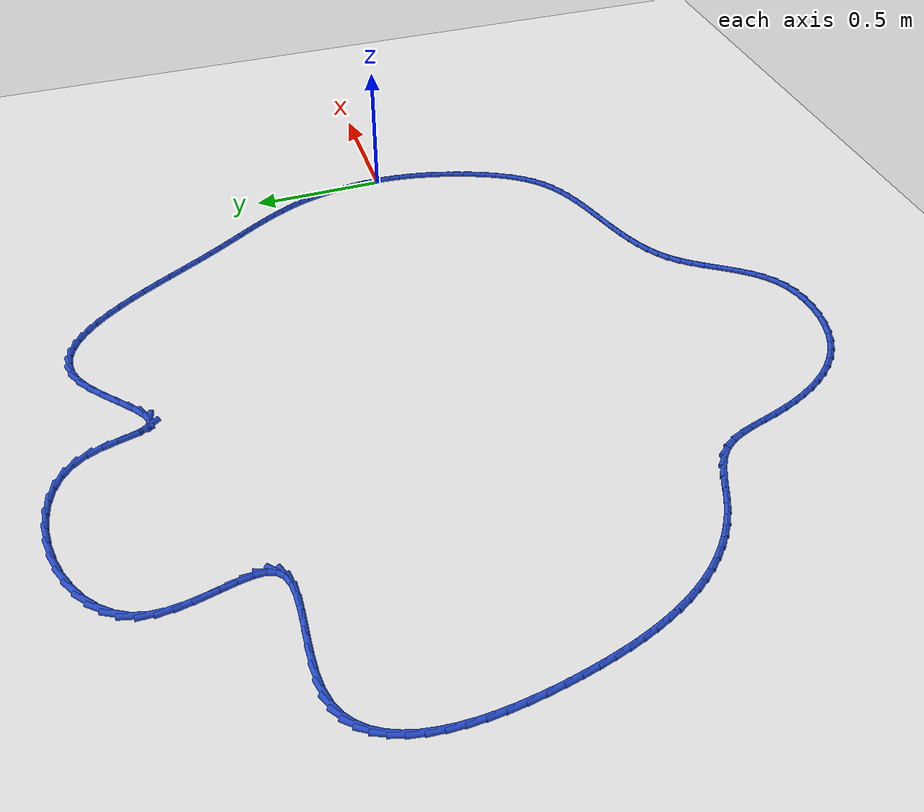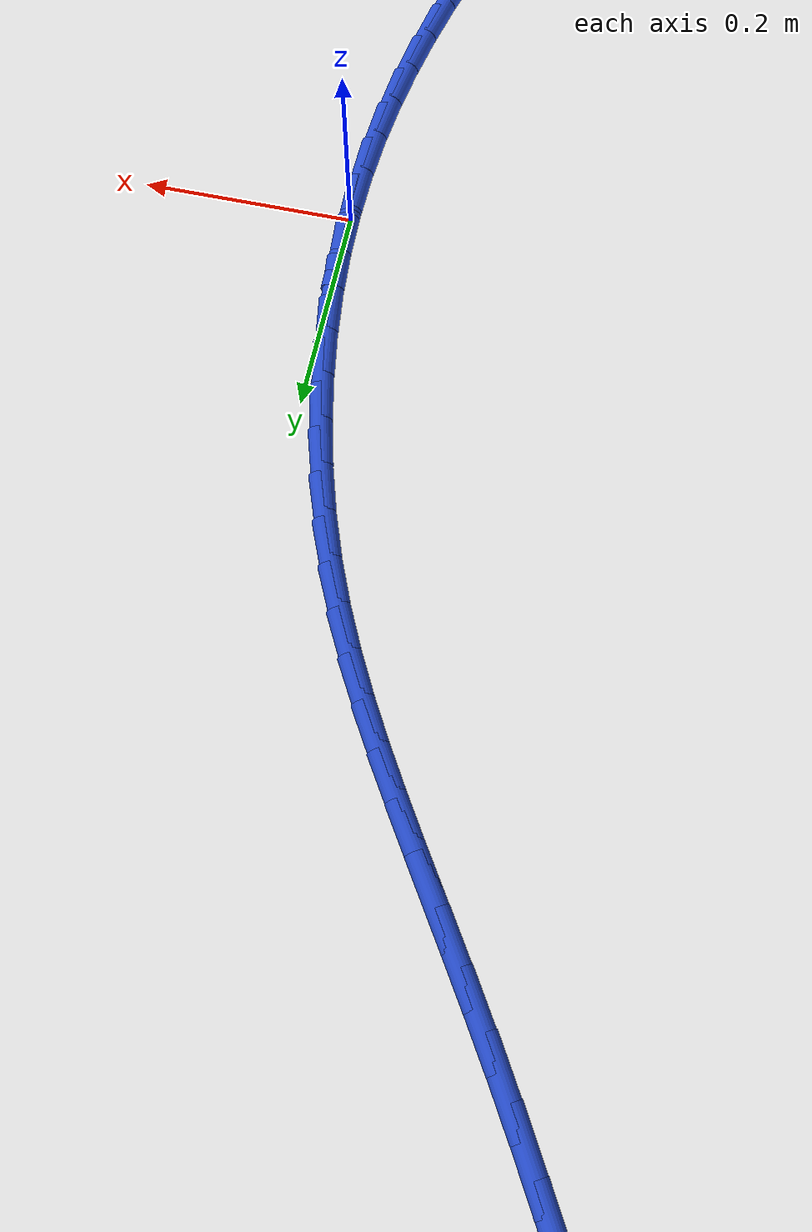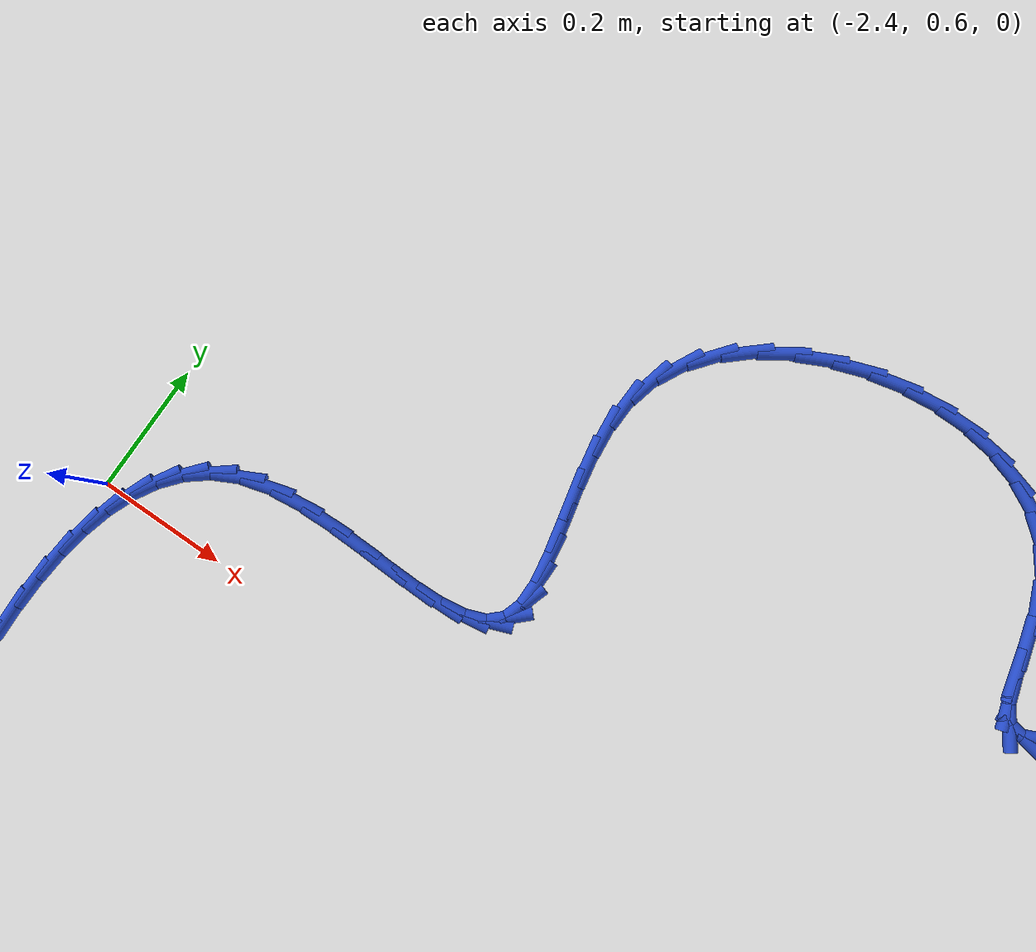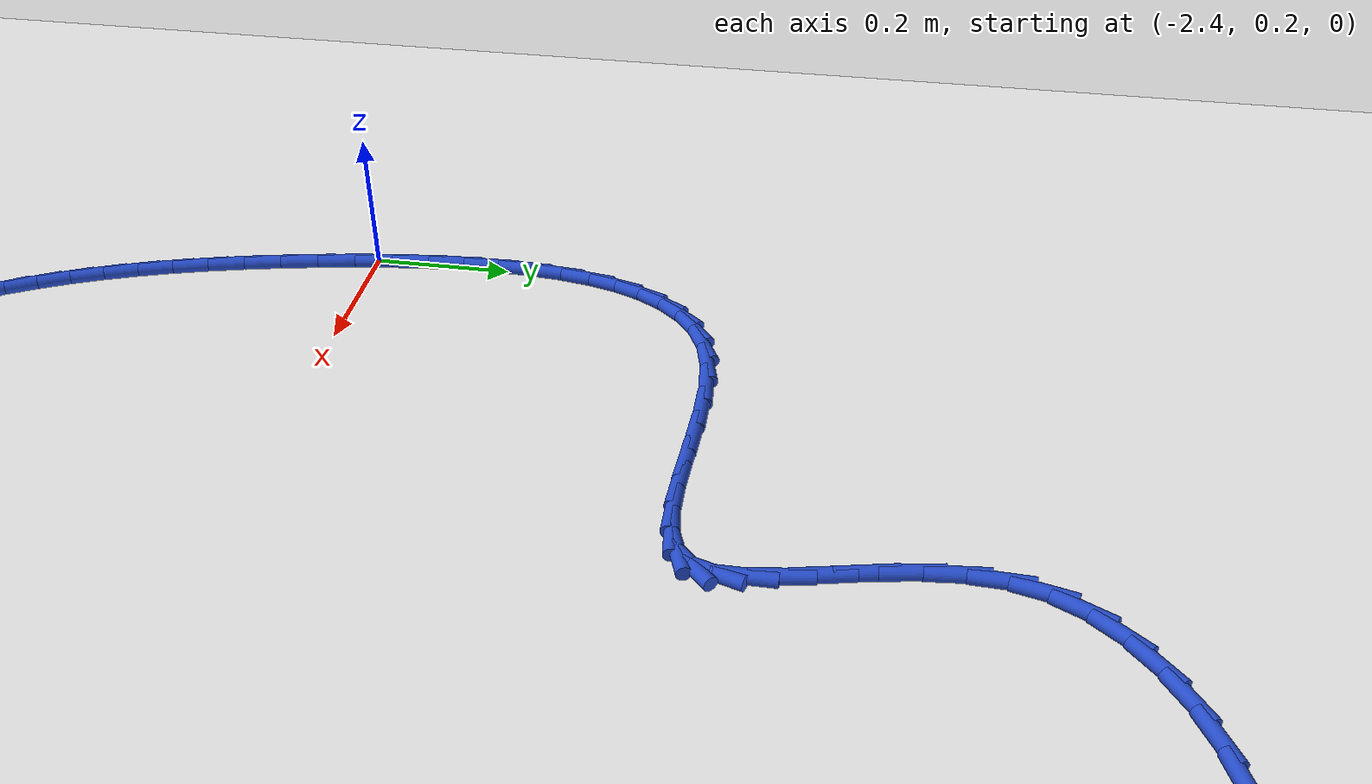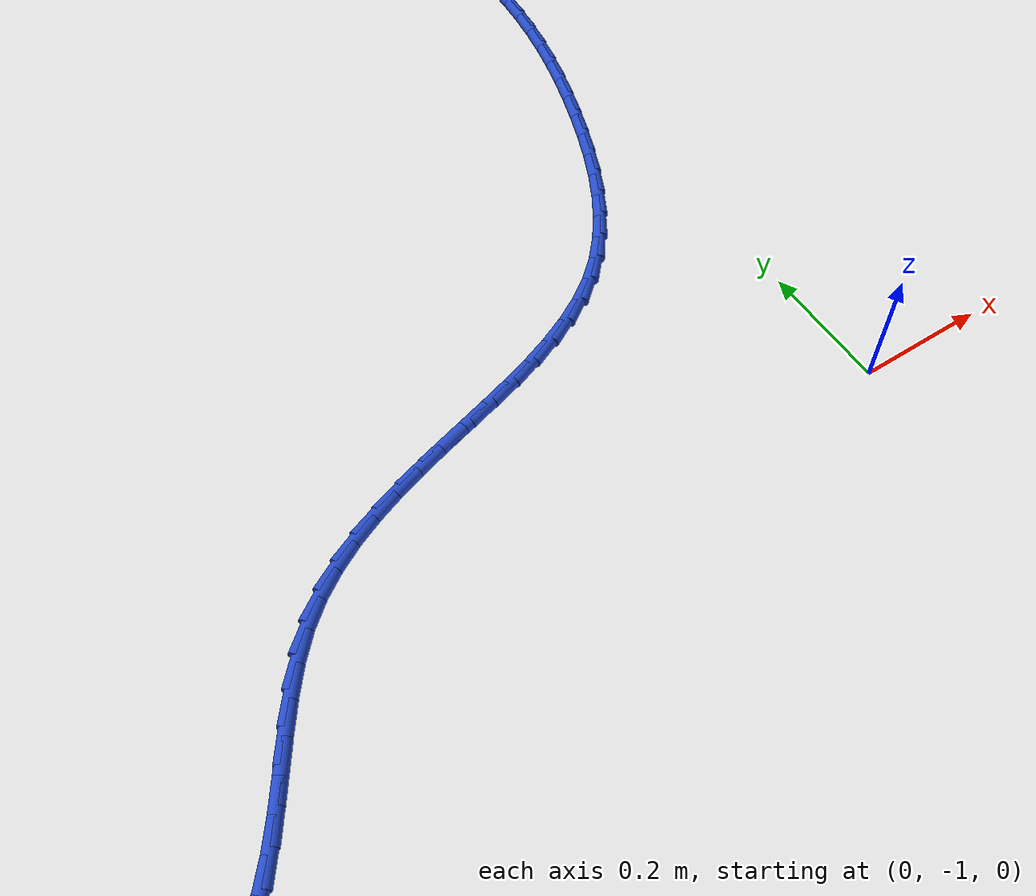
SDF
<sdf version="1.6">
 <world name="default">
  <light name="sun" type="directional">
   <pose>0 0 10 0 -0 0</pose>
   <diffuse>0.8 0.8 0.8 1</diffuse>
   <specular>0.2 0.2 0.2 1</specular>
   <attenuation>
    <range>1000</range>
    <constant>0.9</constant>
    <linear>0.01</linear>
    <quadratic>0.001</quadratic>
   </attenuation>
   <direction>-0.5 0.1 -0.9</direction>
  </light>
  <model name="ground_plane">
   <static>1</static>
   <link name="link">
    <collision name="collision">
     <geometry><plane><normal>0 0 1</normal><size>100 100</size></plane></geometry>
     <surface><friction><ode><mu>100</mu><mu2>50</mu2></ode></friction></surface>
    </collision>
    <visual name="visual">
     <cast_shadows>0</cast_shadows>
     <geometry><plane><normal>0 0 1</normal><size>100 100</size></plane></geometry>
     <material>
      <script><uri>file://media/materials/scripts/gazebo.material</uri><name>Gazebo/WhiteGlow</name></script>
     </material>
    </visual>
   </link>
  </model>
  <gravity>0 0 -9.8</gravity>
  <magnetic_field>6e-06 2.3e-05 -4.2e-05</magnetic_field>
  <atmosphere type="adiabatic"/>
  <physics name="default_physics" default="0" type="ode">
   <max_step_size>0.001</max_step_size>
   <real_time_factor>1</real_time_factor>
   <real_time_update_rate>1000</real_time_update_rate>
  </physics>
  <scene><ambient>0.4 0.4 0.4 1</ambient><background>0.7 0.7 0.7 1</background><shadows>1</shadows></scene>
  <spherical_coordinates>
   <surface_model>EARTH_WGS84</surface_model>
   <latitude_deg>0</latitude_deg>
   <longitude_deg>0</longitude_deg>
   <elevation>0</elevation>
   <heading_deg>0</heading_deg>
  </spherical_coordinates>
  <model name="line">
   <link name="link_0">
    <pose>-1.214306433183765e-17 -2.0816681711721685e-17 0.01 0 1.57 -1.5514804229503802</pose>
    <collision name="collision">
     <geometry><cylinder><radius>0.01</radius><length>0.08</length></cylinder></geometry>
    </collision>
    <visual name="visual">
     <material>
      <script><name>Gazebo/Blue</name><uri>file://media/materials/scripts/gazebo.material</uri></script>
     </material>
     <geometry><cylinder><radius>0.01</radius><length>0.08</length></cylinder></geometry>
    </visual>
   </link>
   <link name="link_1">
    <pose>-0.0008678426783834466 0.04492333109464694 0.01 0 1.57 -1.5049221918385318</pose>
    <collision name="collision">
     <geometry><cylinder><radius>0.01</radius><length>0.08</length></cylinder></geometry>
    </collision>
    <visual name="visual">
     <material>
      <script><name>Gazebo/Blue</name><uri>file://media/materials/scripts/gazebo.material</uri></script>
     </material>
     <geometry><cylinder><radius>0.01</radius><length>0.08</length></cylinder></geometry>
    </visual>
   </link>
   <link name="link_2">
    <pose>-0.003843669696837276 0.09003240673459685 0.01 0 1.57 -1.4595242195928066</pose>
    <collision name="collision">
     <geometry><cylinder><radius>0.01</radius><length>0.08</length></cylinder></geometry>
    </collision>
    <visual name="visual">
     <material>
      <script><name>Gazebo/Blue</name><uri>file://media/materials/scripts/gazebo.material</uri></script>
     </material>
     <geometry><cylinder><radius>0.01</radius><length>0.08</length></cylinder></geometry>
    </visual>
   </link>
   <link name="link_3">
    <pose>-0.008873220678676763 0.13504616794314886 0.01 0 1.57 -1.4146096449957104</pose>
    <collision name="collision">
     <geometry><cylinder><radius>0.01</radius><length>0.08</length></cylinder></geometry>
    </collision>
    <visual name="visual">
     <material>
      <script><name>Gazebo/Blue</name><uri>file://media/materials/scripts/gazebo.material</uri></script>
     </material>
     <geometry><cylinder><radius>0.01</radius><length>0.08</length></cylinder></geometry>
    </visual>
   </link>
   <link name="link_4">
    <pose>-0.015902235247217178 0.17968355574360206 0.01 0 1.57 -1.3695072316632912</pose>
    <collision name="collision">
     <geometry><cylinder><radius>0.01</radius><length>0.08</length></cylinder></geometry>
    </collision>
    <visual name="visual">
     <material>
      <script><name>Gazebo/Blue</name><uri>file://media/materials/scripts/gazebo.material</uri></script>
     </material>
     <geometry><cylinder><radius>0.01</radius><length>0.08</length></cylinder></geometry>
    </visual>
   </link>
   <link name="link_5">
    <pose>-0.024876453025773772 0.22366351115925545 0.01 0 1.57 -1.323527463527113</pose>
    <collision name="collision">
     <geometry><cylinder><radius>0.01</radius><length>0.08</length></cylinder></geometry>
    </collision>
    <visual name="visual">
     <material>
      <script><name>Gazebo/Blue</name><uri>file://media/materials/scripts/gazebo.material</uri></script>
     </material>
     <geometry><cylinder><radius>0.01</radius><length>0.08</length></cylinder></geometry>
    </visual>
   </link>
   <link name="link_6">
    <pose>-0.0357416136376618 0.26670497521340814 0.01 0 1.57 -1.275936947140723</pose>
    <collision name="collision">
     <geometry><cylinder><radius>0.01</radius><length>0.08</length></cylinder></geometry>
    </collision>
    <visual name="visual">
     <material>
      <script><name>Gazebo/Blue</name><uri>file://media/materials/scripts/gazebo.material</uri></script>
     </material>
     <geometry><cylinder><radius>0.01</radius><length>0.08</length></cylinder></geometry>
    </visual>
   </link>
   <link name="link_7">
    <pose>-0.04844345670619654 0.30852688892935937 0.01 0 1.57 -1.2259362961388207</pose>
    <collision name="collision">
     <geometry><cylinder><radius>0.01</radius><length>0.08</length></cylinder></geometry>
    </collision>
    <visual name="visual">
     <material>
      <script><name>Gazebo/Blue</name><uri>file://media/materials/scripts/gazebo.material</uri></script>
     </material>
     <geometry><cylinder><radius>0.01</radius><length>0.08</length></cylinder></geometry>
    </visual>
   </link>
   <link name="link_8">
    <pose>-0.06292766682589343 0.3488487856903481 0.01 0 1.57 -1.1746973466063533</pose>
    <collision name="collision">
     <geometry><cylinder><radius>0.01</radius><length>0.08</length></cylinder></geometry>
    </collision>
    <visual name="visual">
     <material>
      <script><name>Gazebo/Blue</name><uri>file://media/materials/scripts/gazebo.material</uri></script>
     </material>
     <geometry><cylinder><radius>0.01</radius><length>0.08</length></cylinder></geometry>
    </visual>
   </link>
   <link name="link_9">
    <pose>-0.07912281599990902 0.3875744081233273 0.01 0 1.57 -1.1275314631234585</pose>
    <collision name="collision">
     <geometry><cylinder><radius>0.01</radius><length>0.08</length></cylinder></geometry>
    </collision>
    <visual name="visual">
     <material>
      <script><name>Gazebo/Blue</name><uri>file://media/materials/scripts/gazebo.material</uri></script>
     </material>
     <geometry><cylinder><radius>0.01</radius><length>0.08</length></cylinder></geometry>
    </visual>
   </link>
   <link name="link_10">
    <pose>-0.09691619333019154 0.4250518904643498 0.01 0 1.57 -1.0865978137405188</pose>
    <collision name="collision">
     <geometry><cylinder><radius>0.01</radius><length>0.08</length></cylinder></geometry>
    </collision>
    <visual name="visual">
     <material>
      <script><name>Gazebo/Blue</name><uri>file://media/materials/scripts/gazebo.material</uri></script>
     </material>
     <geometry><cylinder><radius>0.01</radius><length>0.08</length></cylinder></geometry>
    </visual>
   </link>
   <link name="link_11">
    <pose>-0.11618898727631548 0.46169503758311337 0.01 0 1.57 -1.0530089885697747</pose>
    <collision name="collision">
     <geometry><cylinder><radius>0.01</radius><length>0.08</length></cylinder></geometry>
    </collision>
    <visual name="visual">
     <material>
      <script><name>Gazebo/Blue</name><uri>file://media/materials/scripts/gazebo.material</uri></script>
     </material>
     <geometry><cylinder><radius>0.01</radius><length>0.08</length></cylinder></geometry>
    </visual>
   </link>
   <link name="link_12">
    <pose>-0.13682238629785515 0.49791765434931534 0.01 0 1.57 -1.0274247715743958</pose>
    <collision name="collision">
     <geometry><cylinder><radius>0.01</radius><length>0.08</length></cylinder></geometry>
    </collision>
    <visual name="visual">
     <material>
      <script><name>Gazebo/Blue</name><uri>file://media/materials/scripts/gazebo.material</uri></script>
     </material>
     <geometry><cylinder><radius>0.01</radius><length>0.08</length></cylinder></geometry>
    </visual>
   </link>
   <link name="link_13">
    <pose>-0.15869757885438512 0.5341335456326539 0.01 0 1.57 -1.0100631980832475</pose>
    <collision name="collision">
     <geometry><cylinder><radius>0.01</radius><length>0.08</length></cylinder></geometry>
    </collision>
    <visual name="visual">
     <material>
      <script><name>Gazebo/Blue</name><uri>file://media/materials/scripts/gazebo.material</uri></script>
     </material>
     <geometry><cylinder><radius>0.01</radius><length>0.08</length></cylinder></geometry>
    </visual>
   </link>
   <link name="link_14">
    <pose>-0.1816957534054798 0.5707565163028264 0.01 0 1.57 -1.000758250028578</pose>
    <collision name="collision">
     <geometry><cylinder><radius>0.01</radius><length>0.08</length></cylinder></geometry>
    </collision>
    <visual name="visual">
     <material>
      <script><name>Gazebo/Blue</name><uri>file://media/materials/scripts/gazebo.material</uri></script>
     </material>
     <geometry><cylinder><radius>0.01</radius><length>0.08</length></cylinder></geometry>
    </visual>
   </link>
   <link name="link_15">
    <pose>-0.2056980984107136 0.6082003712295306 0.01 0 1.57 -0.9990395615238913</pose>
    <collision name="collision">
     <geometry><cylinder><radius>0.01</radius><length>0.08</length></cylinder></geometry>
    </collision>
    <visual name="visual">
     <material>
      <script><name>Gazebo/Blue</name><uri>file://media/materials/scripts/gazebo.material</uri></script>
     </material>
     <geometry><cylinder><radius>0.01</radius><length>0.08</length></cylinder></geometry>
    </visual>
   </link>
   <link name="link_16">
    <pose>-0.2305858023296609 0.6468789152824641 0.01 0 1.57 -1.0042155455910822</pose>
    <collision name="collision">
     <geometry><cylinder><radius>0.01</radius><length>0.08</length></cylinder></geometry>
    </collision>
    <visual name="visual">
     <material>
      <script><name>Gazebo/Blue</name><uri>file://media/materials/scripts/gazebo.material</uri></script>
     </material>
     <geometry><cylinder><radius>0.01</radius><length>0.08</length></cylinder></geometry>
    </visual>
   </link>
   <link name="link_17">
    <pose>-0.2562400536218963 0.6872059533313248 0.01 0 1.57 -1.0154496720061035</pose>
    <collision name="collision">
     <geometry><cylinder><radius>0.01</radius><length>0.08</length></cylinder></geometry>
    </collision>
    <visual name="visual">
     <material>
      <script><name>Gazebo/Blue</name><uri>file://media/materials/scripts/gazebo.material</uri></script>
     </material>
     <geometry><cylinder><radius>0.01</radius><length>0.08</length></cylinder></geometry>
    </visual>
   </link>
   <link name="link_18">
    <pose>-0.2825420407469941 0.7295952902458105 0.01 0 1.57 -1.0316831990888369</pose>
    <collision name="collision">
     <geometry><cylinder><radius>0.01</radius><length>0.08</length></cylinder></geometry>
    </collision>
    <visual name="visual">
     <material>
      <script><name>Gazebo/Blue</name><uri>file://media/materials/scripts/gazebo.material</uri></script>
     </material>
     <geometry><cylinder><radius>0.01</radius><length>0.08</length></cylinder></geometry>
    </visual>
   </link>
   <link name="link_19">
    <pose>-0.3093745821889473 0.7744489052406198 0.01 0 1.57 -1.046342045684514</pose>
    <collision name="collision">
     <geometry><cylinder><radius>0.01</radius><length>0.08</length></cylinder></geometry>
    </collision>
    <visual name="visual">
     <material>
      <script><name>Gazebo/Blue</name><uri>file://media/materials/scripts/gazebo.material</uri></script>
     </material>
     <geometry><cylinder><radius>0.01</radius><length>0.08</length></cylinder></geometry>
    </visual>
   </link>
   <link name="link_20">
    <pose>-0.336689696716729 0.8216667367716824 0.01 0 1.57 -1.052345552330536</pose>
    <collision name="collision">
     <geometry><cylinder><radius>0.01</radius><length>0.08</length></cylinder></geometry>
    </collision>
    <visual name="visual">
     <material>
      <script><name>Gazebo/Blue</name><uri>file://media/materials/scripts/gazebo.material</uri></script>
     </material>
     <geometry><cylinder><radius>0.01</radius><length>0.08</length></cylinder></geometry>
    </visual>
   </link>
   <link name="link_21">
    <pose>-0.3645328248226546 0.8704709585590314 0.01 0 1.57 -1.0501239331744157</pose>
    <collision name="collision">
     <geometry><cylinder><radius>0.01</radius><length>0.08</length></cylinder></geometry>
    </collision>
    <visual name="visual">
     <material>
      <script><name>Gazebo/Blue</name><uri>file://media/materials/scripts/gazebo.material</uri></script>
     </material>
     <geometry><cylinder><radius>0.01</radius><length>0.08</length></cylinder></geometry>
    </visual>
   </link>
   <link name="link_22">
    <pose>-0.39295601850467876 0.9200357785475892 0.01 0 1.57 -1.0400050564200711</pose>
    <collision name="collision">
     <geometry><cylinder><radius>0.01</radius><length>0.08</length></cylinder></geometry>
    </collision>
    <visual name="visual">
     <material>
      <script><name>Gazebo/Blue</name><uri>file://media/materials/scripts/gazebo.material</uri></script>
     </material>
     <geometry><cylinder><radius>0.01</radius><length>0.08</length></cylinder></geometry>
    </visual>
   </link>
   <link name="link_23">
    <pose>-0.42201132976075495 0.9695354046822767 0.01 0 1.57 -1.02173480589715</pose>
    <collision name="collision">
     <geometry><cylinder><radius>0.01</radius><length>0.08</length></cylinder></geometry>
    </collision>
    <visual name="visual">
     <material>
      <script><name>Gazebo/Blue</name><uri>file://media/materials/scripts/gazebo.material</uri></script>
     </material>
     <geometry><cylinder><radius>0.01</radius><length>0.08</length></cylinder></geometry>
    </visual>
   </link>
   <link name="link_24">
    <pose>-0.4517508105888372 1.0181440449080152 0.01 0 1.57 -0.9944811962762646</pose>
    <collision name="collision">
     <geometry><cylinder><radius>0.01</radius><length>0.08</length></cylinder></geometry>
    </collision>
    <visual name="visual">
     <material>
      <script><name>Gazebo/Blue</name><uri>file://media/materials/scripts/gazebo.material</uri></script>
     </material>
     <geometry><cylinder><radius>0.01</radius><length>0.08</length></cylinder></geometry>
    </visual>
   </link>
   <link name="link_25">
    <pose>-0.4822265129868798 1.0650359071697262 0.01 0 1.57 -0.956756802255527</pose>
    <collision name="collision">
     <geometry><cylinder><radius>0.01</radius><length>0.08</length></cylinder></geometry>
    </collision>
    <visual name="visual">
     <material>
      <script><name>Gazebo/Blue</name><uri>file://media/materials/scripts/gazebo.material</uri></script>
     </material>
     <geometry><cylinder><radius>0.01</radius><length>0.08</length></cylinder></geometry>
    </visual>
   </link>
   <link name="link_26">
    <pose>-0.5134904889528366 1.1093851994123316 0.01 0 1.57 -0.9062620205907913</pose>
    <collision name="collision">
     <geometry><cylinder><radius>0.01</radius><length>0.08</length></cylinder></geometry>
    </collision>
    <visual name="visual">
     <material>
      <script><name>Gazebo/Blue</name><uri>file://media/materials/scripts/gazebo.material</uri></script>
     </material>
     <geometry><cylinder><radius>0.01</radius><length>0.08</length></cylinder></geometry>
    </visual>
   </link>
   <link name="link_27">
    <pose>-0.5455947904846612 1.1503661295807512 0.01 0 1.57 -0.8396571108135491</pose>
    <collision name="collision">
     <geometry><cylinder><radius>0.01</radius><length>0.08</length></cylinder></geometry>
    </collision>
    <visual name="visual">
     <material>
      <script><name>Gazebo/Blue</name><uri>file://media/materials/scripts/gazebo.material</uri></script>
     </material>
     <geometry><cylinder><radius>0.01</radius><length>0.08</length></cylinder></geometry>
    </visual>
   </link>
   <link name="link_28">
    <pose>-0.5785914695803083 1.1871529056199086 0.01 0 1.57 -0.7523201853578677</pose>
    <collision name="collision">
     <geometry><cylinder><radius>0.01</radius><length>0.08</length></cylinder></geometry>
    </collision>
    <visual name="visual">
     <material>
      <script><name>Gazebo/Blue</name><uri>file://media/materials/scripts/gazebo.material</uri></script>
     </material>
     <geometry><cylinder><radius>0.01</radius><length>0.08</length></cylinder></geometry>
    </visual>
   </link>
   <link name="link_29">
    <pose>-0.6125325782377311 1.2189197354747232 0.01 0 1.57 -0.6383134153249803</pose>
    <collision name="collision">
     <geometry><cylinder><radius>0.01</radius><length>0.08</length></cylinder></geometry>
    </collision>
    <visual name="visual">
     <material>
      <script><name>Gazebo/Blue</name><uri>file://media/materials/scripts/gazebo.material</uri></script>
     </material>
     <geometry><cylinder><radius>0.01</radius><length>0.08</length></cylinder></geometry>
    </visual>
   </link>
   <link name="link_30">
    <pose>-0.6474701684548845 1.2448408270901177 0.01 0 1.57 -0.4911888678127841</pose>
    <collision name="collision">
     <geometry><cylinder><radius>0.01</radius><length>0.08</length></cylinder></geometry>
    </collision>
    <visual name="visual">
     <material>
      <script><name>Gazebo/Blue</name><uri>file://media/materials/scripts/gazebo.material</uri></script>
     </material>
     <geometry><cylinder><radius>0.01</radius><length>0.08</length></cylinder></geometry>
    </visual>
   </link>
   <link name="link_31">
    <pose>-0.6834562922297214 1.2640903884110122 0.01 0 1.57 -0.30687516031156037</pose>
    <collision name="collision">
     <geometry><cylinder><radius>0.01</radius><length>0.08</length></cylinder></geometry>
    </collision>
    <visual name="visual">
     <material>
      <script><name>Gazebo/Blue</name><uri>file://media/materials/scripts/gazebo.material</uri></script>
     </material>
     <geometry><cylinder><radius>0.01</radius><length>0.08</length></cylinder></geometry>
    </visual>
   </link>
   <link name="link_32">
    <pose>-0.7205430015601966 1.2758426273823291 0.01 0 1.57 -0.08943606505969601</pose>
    <collision name="collision">
     <geometry><cylinder><radius>0.01</radius><length>0.08</length></cylinder></geometry>
    </collision>
    <visual name="visual">
     <material>
      <script><name>Gazebo/Blue</name><uri>file://media/materials/scripts/gazebo.material</uri></script>
     </material>
     <geometry><cylinder><radius>0.01</radius><length>0.08</length></cylinder></geometry>
    </visual>
   </link>
   <link name="link_33">
    <pose>-0.7587823484442638 1.2792717519489896 0.01 0 1.57 0.14400626964484264</pose>
    <collision name="collision">
     <geometry><cylinder><radius>0.01</radius><length>0.08</length></cylinder></geometry>
    </collision>
    <visual name="visual">
     <material>
      <script><name>Gazebo/Blue</name><uri>file://media/materials/scripts/gazebo.material</uri></script>
     </material>
     <geometry><cylinder><radius>0.01</radius><length>0.08</length></cylinder></geometry>
    </visual>
   </link>
   <link name="link_34">
    <pose>-0.7982263848798768 1.2735519700559146 0.01 0 1.57 0.36803685280434095</pose>
    <collision name="collision">
     <geometry><cylinder><radius>0.01</radius><length>0.08</length></cylinder></geometry>
    </collision>
    <visual name="visual">
     <material>
      <script><name>Gazebo/Blue</name><uri>file://media/materials/scripts/gazebo.material</uri></script>
     </material>
     <geometry><cylinder><radius>0.01</radius><length>0.08</length></cylinder></geometry>
    </visual>
   </link>
   <link name="link_35">
    <pose>-0.8389271628649898 1.2578574896480257 0.01 0 1.57 0.5590238708364674</pose>
    <collision name="collision">
     <geometry><cylinder><radius>0.01</radius><length>0.08</length></cylinder></geometry>
    </collision>
    <visual name="visual">
     <material>
      <script><name>Gazebo/Blue</name><uri>file://media/materials/scripts/gazebo.material</uri></script>
     </material>
     <geometry><cylinder><radius>0.01</radius><length>0.08</length></cylinder></geometry>
    </visual>
   </link>
   <link name="link_36">
    <pose>-0.8808785465923011 1.2316131002517736 0.01 0 1.57 0.6812065364617392</pose>
    <collision name="collision">
     <geometry><cylinder><radius>0.01</radius><length>0.08</length></cylinder></geometry>
    </collision>
    <visual name="visual">
     <material>
      <script><name>Gazebo/Blue</name><uri>file://media/materials/scripts/gazebo.material</uri></script>
     </material>
     <geometry><cylinder><radius>0.01</radius><length>0.08</length></cylinder></geometry>
    </visual>
   </link>
   <link name="link_37">
    <pose>-0.9234014703211174 1.197141515558739 0.01 0 1.57 0.7423256621221415</pose>
    <collision name="collision">
     <geometry><cylinder><radius>0.01</radius><length>0.08</length></cylinder></geometry>
    </collision>
    <visual name="visual">
     <material>
      <script><name>Gazebo/Blue</name><uri>file://media/materials/scripts/gazebo.material</uri></script>
     </material>
     <geometry><cylinder><radius>0.01</radius><length>0.08</length></cylinder></geometry>
    </visual>
   </link>
   <link name="link_38">
    <pose>-0.9653843777014977 1.1586279388386032 0.01 0 1.57 0.7601751829311802</pose>
    <collision name="collision">
     <geometry><cylinder><radius>0.01</radius><length>0.08</length></cylinder></geometry>
    </collision>
    <visual name="visual">
     <material>
      <script><name>Gazebo/Blue</name><uri>file://media/materials/scripts/gazebo.material</uri></script>
     </material>
     <geometry><cylinder><radius>0.01</radius><length>0.08</length></cylinder></geometry>
    </visual>
   </link>
   <link name="link_39">
    <pose>-1.0057085783200055 1.1202882956903337 0.01 0 1.57 0.7351301806686831</pose>
    <collision name="collision">
     <geometry><cylinder><radius>0.01</radius><length>0.08</length></cylinder></geometry>
    </collision>
    <visual name="visual">
     <material>
      <script><name>Gazebo/Blue</name><uri>file://media/materials/scripts/gazebo.material</uri></script>
     </material>
     <geometry><cylinder><radius>0.01</radius><length>0.08</length></cylinder></geometry>
    </visual>
   </link>
   <link name="link_40">
    <pose>-1.043255381763203 1.0863385117128987 0.01 0 1.57 0.6455133526023412</pose>
    <collision name="collision">
     <geometry><cylinder><radius>0.01</radius><length>0.08</length></cylinder></geometry>
    </collision>
    <visual name="visual">
     <material>
      <script><name>Gazebo/Blue</name><uri>file://media/materials/scripts/gazebo.material</uri></script>
     </material>
     <geometry><cylinder><radius>0.01</radius><length>0.08</length></cylinder></geometry>
    </visual>
   </link>
   <link name="link_41">
    <pose>-1.0769060976176543 1.0609945125052669 0.01 0 1.57 0.4122364984934526</pose>
    <collision name="collision">
     <geometry><cylinder><radius>0.01</radius><length>0.08</length></cylinder></geometry>
    </collision>
    <visual name="visual">
     <material>
      <script><name>Gazebo/Blue</name><uri>file://media/materials/scripts/gazebo.material</uri></script>
     </material>
     <geometry><cylinder><radius>0.01</radius><length>0.08</length></cylinder></geometry>
    </visual>
   </link>
   <link name="link_42">
    <pose>-1.1055420354699221 1.0484722236664064 0.01 0 1.57 -0.1980250252172087</pose>
    <collision name="collision">
     <geometry><cylinder><radius>0.01</radius><length>0.08</length></cylinder></geometry>
    </collision>
    <visual name="visual">
     <material>
      <script><name>Gazebo/Blue</name><uri>file://media/materials/scripts/gazebo.material</uri></script>
     </material>
     <geometry><cylinder><radius>0.01</radius><length>0.08</length></cylinder></geometry>
    </visual>
   </link>
   <link name="link_43">
    <pose>-1.1280445529842147 1.0529874601636637 0.01 0 1.57 -0.9780239369295793</pose>
    <collision name="collision">
     <geometry><cylinder><radius>0.01</radius><length>0.08</length></cylinder></geometry>
    </collision>
    <visual name="visual">
     <material>
      <script><name>Gazebo/Blue</name><uri>file://media/materials/scripts/gazebo.material</uri></script>
     </material>
     <geometry><cylinder><radius>0.01</radius><length>0.08</length></cylinder></geometry>
    </visual>
   </link>
   <link name="link_44">
    <pose>-1.1441211739523374 1.0768549434993822 0.01 0 1.57 -1.2640708413131694</pose>
    <collision name="collision">
     <geometry><cylinder><radius>0.01</radius><length>0.08</length></cylinder></geometry>
    </collision>
    <visual name="visual">
     <material>
      <script><name>Gazebo/Blue</name><uri>file://media/materials/scripts/gazebo.material</uri></script>
     </material>
     <geometry><cylinder><radius>0.01</radius><length>0.08</length></cylinder></geometry>
    </visual>
   </link>
   <link name="link_45">
    <pose>-1.1564082960580762 1.1156497542854311 0.01 0 1.57 -1.3291346633051313</pose>
    <collision name="collision">
     <geometry><cylinder><radius>0.01</radius><length>0.08</length></cylinder></geometry>
    </collision>
    <visual name="visual">
     <material>
      <script><name>Gazebo/Blue</name><uri>file://media/materials/scripts/gazebo.material</uri></script>
     </material>
     <geometry><cylinder><radius>0.01</radius><length>0.08</length></cylinder></geometry>
    </visual>
   </link>
   <link name="link_46">
    <pose>-1.1681910574448797 1.1634541544291297 0.01 0 1.57 -1.292101575617849</pose>
    <collision name="collision">
     <geometry><cylinder><radius>0.01</radius><length>0.08</length></cylinder></geometry>
    </collision>
    <visual name="visual">
     <material>
      <script><name>Gazebo/Blue</name><uri>file://media/materials/scripts/gazebo.material</uri></script>
     </material>
     <geometry><cylinder><radius>0.01</radius><length>0.08</length></cylinder></geometry>
    </visual>
   </link>
   <link name="link_47">
    <pose>-1.1827545962561936 1.2143504058377932 0.01 0 1.57 -1.1654148411064849</pose>
    <collision name="collision">
     <geometry><cylinder><radius>0.01</radius><length>0.08</length></cylinder></geometry>
    </collision>
    <visual name="visual">
     <material>
      <script><name>Gazebo/Blue</name><uri>file://media/materials/scripts/gazebo.material</uri></script>
     </material>
     <geometry><cylinder><radius>0.01</radius><length>0.08</length></cylinder></geometry>
    </visual>
   </link>
   <link name="link_48">
    <pose>-1.203384050635466 1.2624207704187398 0.01 0 1.57 -0.9416268437969945</pose>
    <collision name="collision">
     <geometry><cylinder><radius>0.01</radius><length>0.08</length></cylinder></geometry>
    </collision>
    <visual name="visual">
     <material>
      <script><name>Gazebo/Blue</name><uri>file://media/materials/scripts/gazebo.material</uri></script>
     </material>
     <geometry><cylinder><radius>0.01</radius><length>0.08</length></cylinder></geometry>
    </visual>
   </link>
   <link name="link_49">
    <pose>-1.2326749468602896 1.3026641707522642 0.01 0 1.57 -0.7013962446543137</pose>
    <collision name="collision">
     <geometry><cylinder><radius>0.01</radius><length>0.08</length></cylinder></geometry>
    </collision>
    <visual name="visual">
     <material>
      <script><name>Gazebo/Blue</name><uri>file://media/materials/scripts/gazebo.material</uri></script>
     </material>
     <geometry><cylinder><radius>0.01</radius><length>0.08</length></cylinder></geometry>
    </visual>
   </link>
   <link name="link_50">
    <pose>-1.2700789364898222 1.3342584979919336 0.01 0 1.57 -0.4865525751029142</pose>
    <collision name="collision">
     <geometry><cylinder><radius>0.01</radius><length>0.08</length></cylinder></geometry>
    </collision>
    <visual name="visual">
     <material>
      <script><name>Gazebo/Blue</name><uri>file://media/materials/scripts/gazebo.material</uri></script>
     </material>
     <geometry><cylinder><radius>0.01</radius><length>0.08</length></cylinder></geometry>
    </visual>
   </link>
   <link name="link_51">
    <pose>-1.3141522512428123 1.357571872453758 0.01 0 1.57 -0.3027878740314888</pose>
    <collision name="collision">
     <geometry><cylinder><radius>0.01</radius><length>0.08</length></cylinder></geometry>
    </collision>
    <visual name="visual">
     <material>
      <script><name>Gazebo/Blue</name><uri>file://media/materials/scripts/gazebo.material</uri></script>
     </material>
     <geometry><cylinder><radius>0.01</radius><length>0.08</length></cylinder></geometry>
    </visual>
   </link>
   <link name="link_52">
    <pose>-1.3634510577462793 1.3729725009763747 0.01 0 1.57 -0.14693671564721333</pose>
    <collision name="collision">
     <geometry><cylinder><radius>0.01</radius><length>0.08</length></cylinder></geometry>
    </collision>
    <visual name="visual">
     <material>
      <script><name>Gazebo/Blue</name><uri>file://media/materials/scripts/gazebo.material</uri></script>
     </material>
     <geometry><cylinder><radius>0.01</radius><length>0.08</length></cylinder></geometry>
    </visual>
   </link>
   <link name="link_53">
    <pose>-1.4165315226272397 1.380828590398421 0.01 0 1.57 -0.012265320240938129</pose>
    <collision name="collision">
     <geometry><cylinder><radius>0.01</radius><length>0.08</length></cylinder></geometry>
    </collision>
    <visual name="visual">
     <material>
      <script><name>Gazebo/Blue</name><uri>file://media/materials/scripts/gazebo.material</uri></script>
     </material>
     <geometry><cylinder><radius>0.01</radius><length>0.08</length></cylinder></geometry>
    </visual>
   </link>
   <link name="link_54">
    <pose>-1.471949812512712 1.3815083475585341 0.01 0 1.57 0.10840165977665855</pose>
    <collision name="collision">
     <geometry><cylinder><radius>0.01</radius><length>0.08</length></cylinder></geometry>
    </collision>
    <visual name="visual">
     <material>
      <script><name>Gazebo/Blue</name><uri>file://media/materials/scripts/gazebo.material</uri></script>
     </material>
     <geometry><cylinder><radius>0.01</radius><length>0.08</length></cylinder></geometry>
    </visual>
   </link>
   <link name="link_55">
    <pose>-1.5282620940297142 1.3753799792953505 0.01 0 1.57 0.22168545761386874</pose>
    <collision name="collision">
     <geometry><cylinder><radius>0.01</radius><length>0.08</length></cylinder></geometry>
    </collision>
    <visual name="visual">
     <material>
      <script><name>Gazebo/Blue</name><uri>file://media/materials/scripts/gazebo.material</uri></script>
     </material>
     <geometry><cylinder><radius>0.01</radius><length>0.08</length></cylinder></geometry>
    </visual>
   </link>
   <link name="link_56">
    <pose>-1.584024533805264 1.3628116924475089 0.01 0 1.57 0.3337048359486734</pose>
    <collision name="collision">
     <geometry><cylinder><radius>0.01</radius><length>0.08</length></cylinder></geometry>
    </collision>
    <visual name="visual">
     <material>
      <script><name>Gazebo/Blue</name><uri>file://media/materials/scripts/gazebo.material</uri></script>
     </material>
     <geometry><cylinder><radius>0.01</radius><length>0.08</length></cylinder></geometry>
    </visual>
   </link>
   <link name="link_57">
    <pose>-1.6377932984663797 1.3441716938536459 0.01 0 1.57 0.4504950071396251</pose>
    <collision name="collision">
     <geometry><cylinder><radius>0.01</radius><length>0.08</length></cylinder></geometry>
    </collision>
    <visual name="visual">
     <material>
      <script><name>Gazebo/Blue</name><uri>file://media/materials/scripts/gazebo.material</uri></script>
     </material>
     <geometry><cylinder><radius>0.01</radius><length>0.08</length></cylinder></geometry>
    </visual>
   </link>
   <link name="link_58">
    <pose>-1.688124554640079 1.3198281903523983 0.01 0 1.57 0.578481409554617</pose>
    <collision name="collision">
     <geometry><cylinder><radius>0.01</radius><length>0.08</length></cylinder></geometry>
    </collision>
    <visual name="visual">
     <material>
      <script><name>Gazebo/Blue</name><uri>file://media/materials/scripts/gazebo.material</uri></script>
     </material>
     <geometry><cylinder><radius>0.01</radius><length>0.08</length></cylinder></geometry>
    </visual>
   </link>
   <link name="link_59">
    <pose>-1.7335744689533792 1.2901493887824045 0.01 0 1.57 0.7247594624763687</pose>
    <collision name="collision">
     <geometry><cylinder><radius>0.01</radius><length>0.08</length></cylinder></geometry>
    </collision>
    <visual name="visual">
     <material>
      <script><name>Gazebo/Blue</name><uri>file://media/materials/scripts/gazebo.material</uri></script>
     </material>
     <geometry><cylinder><radius>0.01</radius><length>0.08</length></cylinder></geometry>
    </visual>
   </link>
   <link name="link_60">
    <pose>-1.7726992080332993 1.2555034959823004 0.01 0 1.57 0.8966786034800135</pose>
    <collision name="collision">
     <geometry><cylinder><radius>0.01</radius><length>0.08</length></cylinder></geometry>
    </collision>
    <visual name="visual">
     <material>
      <script><name>Gazebo/Blue</name><uri>file://media/materials/scripts/gazebo.material</uri></script>
     </material>
     <geometry><cylinder><radius>0.01</radius><length>0.08</length></cylinder></geometry>
    </visual>
   </link>
   <link name="link_61">
    <pose>-1.8040549385068563 1.2162587187907243 0.01 0 1.57 1.0997210971847196</pose>
    <collision name="collision">
     <geometry><cylinder><radius>0.01</radius><length>0.08</length></cylinder></geometry>
    </collision>
    <visual name="visual">
     <material>
      <script><name>Gazebo/Blue</name><uri>file://media/materials/scripts/gazebo.material</uri></script>
     </material>
     <geometry><cylinder><radius>0.01</radius><length>0.08</length></cylinder></geometry>
    </visual>
   </link>
   <link name="link_62">
    <pose>-1.8261978270010681 1.1727832640463127 0.01 0 1.57 1.3297905816344204</pose>
    <collision name="collision">
     <geometry><cylinder><radius>0.01</radius><length>0.08</length></cylinder></geometry>
    </collision>
    <visual name="visual">
     <material>
      <script><name>Gazebo/Blue</name><uri>file://media/materials/scripts/gazebo.material</uri></script>
     </material>
     <geometry><cylinder><radius>0.01</radius><length>0.08</length></cylinder></geometry>
    </visual>
   </link>
   <link name="link_63">
    <pose>-1.8378233380245896 1.1254833539014566 0.01 0 1.57 1.5310241195044374</pose>
    <collision name="collision">
     <geometry><cylinder><radius>0.01</radius><length>0.08</length></cylinder></geometry>
    </collision>
    <visual name="visual">
     <material>
      <script><name>Gazebo/Blue</name><uri>file://media/materials/scripts/gazebo.material</uri></script>
     </material>
     <geometry><cylinder><radius>0.01</radius><length>0.08</length></cylinder></geometry>
    </visual>
   </link>
   <link name="link_64">
    <pose>-1.8398177826068882 1.075363107022802 0.01 0 1.57 -1.4737930724380839</pose>
    <collision name="collision">
     <geometry><cylinder><radius>0.01</radius><length>0.08</length></cylinder></geometry>
    </collision>
    <visual name="visual">
     <material>
      <script><name>Gazebo/Blue</name><uri>file://media/materials/scripts/gazebo.material</uri></script>
     </material>
     <geometry><cylinder><radius>0.01</radius><length>0.08</length></cylinder></geometry>
    </visual>
   </link>
   <link name="link_65">
    <pose>-1.8348101949212914 1.0239022427560611 0.01 0 1.57 -1.3908758804056465</pose>
    <collision name="collision">
     <geometry><cylinder><radius>0.01</radius><length>0.08</length></cylinder></geometry>
    </collision>
    <visual name="visual">
     <material>
      <script><name>Gazebo/Blue</name><uri>file://media/materials/scripts/gazebo.material</uri></script>
     </material>
     <geometry><cylinder><radius>0.01</radius><length>0.08</length></cylinder></geometry>
    </visual>
   </link>
   <link name="link_66">
    <pose>-1.8254778085016299 0.9725936343714031 0.01 0 1.57 -1.3532094024841836</pose>
    <collision name="collision">
     <geometry><cylinder><radius>0.01</radius><length>0.08</length></cylinder></geometry>
    </collision>
    <visual name="visual">
     <material>
      <script><name>Gazebo/Blue</name><uri>file://media/materials/scripts/gazebo.material</uri></script>
     </material>
     <geometry><cylinder><radius>0.01</radius><length>0.08</length></cylinder></geometry>
    </visual>
   </link>
   <link name="link_67">
    <pose>-1.8144978568817351 0.9229301551389989 0.01 0 1.57 -1.3601029662635795</pose>
    <collision name="collision">
     <geometry><cylinder><radius>0.01</radius><length>0.08</length></cylinder></geometry>
    </collision>
    <visual name="visual">
     <material>
      <script><name>Gazebo/Blue</name><uri>file://media/materials/scripts/gazebo.material</uri></script>
     </material>
     <geometry><cylinder><radius>0.01</radius><length>0.08</length></cylinder></geometry>
    </visual>
   </link>
   <link name="link_68">
    <pose>-1.8045475735954397 0.8764046783290185 0.01 0 1.57 -1.4228591618236333</pose>
    <collision name="collision">
     <geometry><cylinder><radius>0.01</radius><length>0.08</length></cylinder></geometry>
    </collision>
    <visual name="visual">
     <material>
      <script><name>Gazebo/Blue</name><uri>file://media/materials/scripts/gazebo.material</uri></script>
     </material>
     <geometry><cylinder><radius>0.01</radius><length>0.08</length></cylinder></geometry>
    </visual>
   </link>
   <link name="link_69">
    <pose>-1.7983041921765737 0.8345100772116315 0.01 0 1.57 1.566861467894986</pose>
    <collision name="collision">
     <geometry><cylinder><radius>0.01</radius><length>0.08</length></cylinder></geometry>
    </collision>
    <visual name="visual">
     <material>
      <script><name>Gazebo/Blue</name><uri>file://media/materials/scripts/gazebo.material</uri></script>
     </material>
     <geometry><cylinder><radius>0.01</radius><length>0.08</length></cylinder></geometry>
    </visual>
   </link>
   <link name="link_70">
    <pose>-1.798444946158969 0.7987392250570088 0.01 0 1.57 1.254894873098034</pose>
    <collision name="collision">
     <geometry><cylinder><radius>0.01</radius><length>0.08</length></cylinder></geometry>
    </collision>
    <visual name="visual">
     <material>
      <script><name>Gazebo/Blue</name><uri>file://media/materials/scripts/gazebo.material</uri></script>
     </material>
     <geometry><cylinder><radius>0.01</radius><length>0.08</length></cylinder></geometry>
    </visual>
   </link>
   <link name="link_71">
    <pose>-1.807647069076457 0.7705849951353196 0.01 0 1.57 0.7593934778313208</pose>
    <collision name="collision">
     <geometry><cylinder><radius>0.01</radius><length>0.08</length></cylinder></geometry>
    </collision>
    <visual name="visual">
     <material>
      <script><name>Gazebo/Blue</name><uri>file://media/materials/scripts/gazebo.material</uri></script>
     </material>
     <geometry><cylinder><radius>0.01</radius><length>0.08</length></cylinder></geometry>
    </visual>
   </link>
   <link name="link_72">
    <pose>-1.8280811310880405 0.7511869871321039 0.01 0 1.57 0.3601617604744319</pose>
    <collision name="collision">
     <geometry><cylinder><radius>0.01</radius><length>0.08</length></cylinder></geometry>
    </collision>
    <visual name="visual">
     <material>
      <script><name>Gazebo/Blue</name><uri>file://media/materials/scripts/gazebo.material</uri></script>
     </material>
     <geometry><cylinder><radius>0.01</radius><length>0.08</length></cylinder></geometry>
    </visual>
   </link>
   <link name="link_73">
    <pose>-1.8589002723474222 0.7395808824958544 0.01 0 1.57 0.14059305659665883</pose>
    <collision name="collision">
     <geometry><cylinder><radius>0.01</radius><length>0.08</length></cylinder></geometry>
    </collision>
    <visual name="visual">
     <material>
      <script><name>Gazebo/Blue</name><uri>file://media/materials/scripts/gazebo.material</uri></script>
     </material>
     <geometry><cylinder><radius>0.01</radius><length>0.08</length></cylinder></geometry>
    </visual>
   </link>
   <link name="link_74">
    <pose>-1.8981451536185112 0.7340266808291177 0.01 0 1.57 0.027198144992063102</pose>
    <collision name="collision">
     <geometry><cylinder><radius>0.01</radius><length>0.08</length></cylinder></geometry>
    </collision>
    <visual name="visual">
     <material>
      <script><name>Gazebo/Blue</name><uri>file://media/materials/scripts/gazebo.material</uri></script>
     </material>
     <geometry><cylinder><radius>0.01</radius><length>0.08</length></cylinder></geometry>
    </visual>
   </link>
   <link name="link_75">
    <pose>-1.9438546831373504 0.7327831597755781 0.01 0 1.57 -0.02640007319044443</pose>
    <collision name="collision">
     <geometry><cylinder><radius>0.01</radius><length>0.08</length></cylinder></geometry>
    </collision>
    <visual name="visual">
     <material>
      <script><name>Gazebo/Blue</name><uri>file://media/materials/scripts/gazebo.material</uri></script>
     </material>
     <geometry><cylinder><radius>0.01</radius><length>0.08</length></cylinder></geometry>
    </visual>
   </link>
   <link name="link_76">
    <pose>-1.9940677691399826 0.7341090969789187 0.01 0 1.57 -0.04081043648398868</pose>
    <collision name="collision">
     <geometry><cylinder><radius>0.01</radius><length>0.08</length></cylinder></geometry>
    </collision>
    <visual name="visual">
     <material>
      <script><name>Gazebo/Blue</name><uri>file://media/materials/scripts/gazebo.material</uri></script>
     </material>
     <geometry><cylinder><radius>0.01</radius><length>0.08</length></cylinder></geometry>
    </visual>
   </link>
   <link name="link_77">
    <pose>-2.046823319862451 0.7362632700828234 0.01 0 1.57 -0.02326648390892616</pose>
    <collision name="collision">
     <geometry><cylinder><radius>0.01</radius><length>0.08</length></cylinder></geometry>
    </collision>
    <visual name="visual">
     <material>
      <script><name>Gazebo/Blue</name><uri>file://media/materials/scripts/gazebo.material</uri></script>
     </material>
     <geometry><cylinder><radius>0.01</radius><length>0.08</length></cylinder></geometry>
    </visual>
   </link>
   <link name="link_78">
    <pose>-2.100160243540797 0.7375044567309758 0.01 0 1.57 0.02718918304557843</pose>
    <collision name="collision">
     <geometry><cylinder><radius>0.01</radius><length>0.08</length></cylinder></geometry>
    </collision>
    <visual name="visual">
     <material>
      <script><name>Gazebo/Blue</name><uri>file://media/materials/scripts/gazebo.material</uri></script>
     </material>
     <geometry><cylinder><radius>0.01</radius><length>0.08</length></cylinder></geometry>
    </visual>
   </link>
   <link name="link_79">
    <pose>-2.152117448411065 0.7360914345670597 0.01 0 1.57 0.11891154176355587</pose>
    <collision name="collision">
     <geometry><cylinder><radius>0.01</radius><length>0.08</length></cylinder></geometry>
    </collision>
    <visual name="visual">
     <material>
      <script><name>Gazebo/Blue</name><uri>file://media/materials/scripts/gazebo.material</uri></script>
     </material>
     <geometry><cylinder><radius>0.01</radius><length>0.08</length></cylinder></geometry>
    </visual>
   </link>
   <link name="link_80">
    <pose>-2.2007338427092966 0.7302829812347585 0.01 0 1.57 0.2680769028519697</pose>
    <collision name="collision">
     <geometry><cylinder><radius>0.01</radius><length>0.08</length></cylinder></geometry>
    </collision>
    <visual name="visual">
     <material>
      <script><name>Gazebo/Blue</name><uri>file://media/materials/scripts/gazebo.material</uri></script>
     </material>
     <geometry><cylinder><radius>0.01</radius><length>0.08</length></cylinder></geometry>
    </visual>
   </link>
   <link name="link_81">
    <pose>-2.2440853555188984 0.7183748045654406 0.01 0 1.57 0.46483263923988277</pose>
    <collision name="collision">
     <geometry><cylinder><radius>0.01</radius><length>0.08</length></cylinder></geometry>
    </collision>
    <visual name="visual">
     <material>
      <script><name>Gazebo/Blue</name><uri>file://media/materials/scripts/gazebo.material</uri></script>
     </material>
     <geometry><cylinder><radius>0.01</radius><length>0.08</length></cylinder></geometry>
    </visual>
   </link>
   <link name="link_82">
    <pose>-2.281300136074665 0.6997122557791133 0.01 0 1.57 0.6706461991000373</pose>
    <collision name="collision">
     <geometry><cylinder><radius>0.01</radius><length>0.08</length></cylinder></geometry>
    </collision>
    <visual name="visual">
     <material>
      <script><name>Gazebo/Blue</name><uri>file://media/materials/scripts/gazebo.material</uri></script>
     </material>
     <geometry><cylinder><radius>0.01</radius><length>0.08</length></cylinder></geometry>
    </visual>
   </link>
   <link name="link_83">
    <pose>-2.3126838680454167 0.6748153368871916 0.01 0 1.57 0.8671831267043318</pose>
    <collision name="collision">
     <geometry><cylinder><radius>0.01</radius><length>0.08</length></cylinder></geometry>
    </collision>
    <visual name="visual">
     <material>
      <script><name>Gazebo/Blue</name><uri>file://media/materials/scripts/gazebo.material</uri></script>
     </material>
     <geometry><cylinder><radius>0.01</radius><length>0.08</length></cylinder></geometry>
    </visual>
   </link>
   <link name="link_84">
    <pose>-2.3386044183181265 0.6442660808398993 0.01 0 1.57 1.0417346272126988</pose>
    <collision name="collision">
     <geometry><cylinder><radius>0.01</radius><length>0.08</length></cylinder></geometry>
    </collision>
    <visual name="visual">
     <material>
      <script><name>Gazebo/Blue</name><uri>file://media/materials/scripts/gazebo.material</uri></script>
     </material>
     <geometry><cylinder><radius>0.01</radius><length>0.08</length></cylinder></geometry>
    </visual>
   </link>
   <link name="link_85">
    <pose>-2.359429653779772 0.60864652058746 0.01 0 1.57 1.1891157607490466</pose>
    <collision name="collision">
     <geometry><cylinder><radius>0.01</radius><length>0.08</length></cylinder></geometry>
    </collision>
    <visual name="visual">
     <material>
      <script><name>Gazebo/Blue</name><uri>file://media/materials/scripts/gazebo.material</uri></script>
     </material>
     <geometry><cylinder><radius>0.01</radius><length>0.08</length></cylinder></geometry>
    </visual>
   </link>
   <link name="link_86">
    <pose>-2.375527441317329 0.5685386890800983 0.01 0 1.57 1.31017015235859</pose>
    <collision name="collision">
     <geometry><cylinder><radius>0.01</radius><length>0.08</length></cylinder></geometry>
    </collision>
    <visual name="visual">
     <material>
      <script><name>Gazebo/Blue</name><uri>file://media/materials/scripts/gazebo.material</uri></script>
     </material>
     <geometry><cylinder><radius>0.01</radius><length>0.08</length></cylinder></geometry>
    </visual>
   </link>
   <link name="link_87">
    <pose>-2.3872656478177747 0.524524619268038 0.01 0 1.57 1.4085927790618753</pose>
    <collision name="collision">
     <geometry><cylinder><radius>0.01</radius><length>0.08</length></cylinder></geometry>
    </collision>
    <visual name="visual">
     <material>
      <script><name>Gazebo/Blue</name><uri>file://media/materials/scripts/gazebo.material</uri></script>
     </material>
     <geometry><cylinder><radius>0.01</radius><length>0.08</length></cylinder></geometry>
    </visual>
   </link>
   <link name="link_88">
    <pose>-2.395012140168083 0.4771863441015016 0.01 0 1.57 1.4886610747038382</pose>
    <collision name="collision">
     <geometry><cylinder><radius>0.01</radius><length>0.08</length></cylinder></geometry>
    </collision>
    <visual name="visual">
     <material>
      <script><name>Gazebo/Blue</name><uri>file://media/materials/scripts/gazebo.material</uri></script>
     </material>
     <geometry><cylinder><radius>0.01</radius><length>0.08</length></cylinder></geometry>
    </visual>
   </link>
   <link name="link_89">
    <pose>-2.399134785255231 0.42710589653071496 0.01 0 1.57 1.5542079753903602</pose>
    <collision name="collision">
     <geometry><cylinder><radius>0.01</radius><length>0.08</length></cylinder></geometry>
    </collision>
    <visual name="visual">
     <material>
      <script><name>Gazebo/Blue</name><uri>file://media/materials/scripts/gazebo.material</uri></script>
     </material>
     <geometry><cylinder><radius>0.01</radius><length>0.08</length></cylinder></geometry>
    </visual>
   </link>
   <link name="link_90">
    <pose>-2.4000014499661955 0.3748653095059009 0.01 0 1.57 -1.5332536284616005</pose>
    <collision name="collision">
     <geometry><cylinder><radius>0.01</radius><length>0.08</length></cylinder></geometry>
    </collision>
    <visual name="visual">
     <material>
      <script><name>Gazebo/Blue</name><uri>file://media/materials/scripts/gazebo.material</uri></script>
     </material>
     <geometry><cylinder><radius>0.01</radius><length>0.08</length></cylinder></geometry>
    </visual>
   </link>
   <link name="link_91">
    <pose>-2.3979800011879524 0.3210466159772836 0.01 0 1.57 -1.4881298246668426</pose>
    <collision name="collision">
     <geometry><cylinder><radius>0.01</radius><length>0.08</length></cylinder></geometry>
    </collision>
    <visual name="visual">
     <material>
      <script><name>Gazebo/Blue</name><uri>file://media/materials/scripts/gazebo.material</uri></script>
     </material>
     <geometry><cylinder><radius>0.01</radius><length>0.08</length></cylinder></geometry>
    </visual>
   </link>
   <link name="link_92">
    <pose>-2.393438305807477 0.26623184889508567 0.01 0 1.57 -1.4501784725371618</pose>
    <collision name="collision">
     <geometry><cylinder><radius>0.01</radius><length>0.08</length></cylinder></geometry>
    </collision>
    <visual name="visual">
     <material>
      <script><name>Gazebo/Blue</name><uri>file://media/materials/scripts/gazebo.material</uri></script>
     </material>
     <geometry><cylinder><radius>0.01</radius><length>0.08</length></cylinder></geometry>
    </visual>
   </link>
   <link name="link_93">
    <pose>-2.3867442307117455 0.2110030412095331 0.01 0 1.57 -1.418010508958739</pose>
    <collision name="collision">
     <geometry><cylinder><radius>0.01</radius><length>0.08</length></cylinder></geometry>
    </collision>
    <visual name="visual">
     <material>
      <script><name>Gazebo/Blue</name><uri>file://media/materials/scripts/gazebo.material</uri></script>
     </material>
     <geometry><cylinder><radius>0.01</radius><length>0.08</length></cylinder></geometry>
    </visual>
   </link>
   <link name="link_94">
    <pose>-2.378265642787734 0.15594222587084877 0.01 0 1.57 -1.3905766749092872</pose>
    <collision name="collision">
     <geometry><cylinder><radius>0.01</radius><length>0.08</length></cylinder></geometry>
    </collision>
    <visual name="visual">
     <material>
      <script><name>Gazebo/Blue</name><uri>file://media/materials/scripts/gazebo.material</uri></script>
     </material>
     <geometry><cylinder><radius>0.01</radius><length>0.08</length></cylinder></geometry>
    </visual>
   </link>
   <link name="link_95">
    <pose>-2.36837040892242 0.1016314358292567 0.01 0 1.57 -1.3668298525879674</pose>
    <collision name="collision">
     <geometry><cylinder><radius>0.01</radius><length>0.08</length></cylinder></geometry>
    </collision>
    <visual name="visual">
     <material>
      <script><name>Gazebo/Blue</name><uri>file://media/materials/scripts/gazebo.material</uri></script>
     </material>
     <geometry><cylinder><radius>0.01</radius><length>0.08</length></cylinder></geometry>
    </visual>
   </link>
   <link name="link_96">
    <pose>-2.3574078660716054 0.04863205361115291 0.01 0 1.57 -1.342612324345396</pose>
    <collision name="collision">
     <geometry><cylinder><radius>0.01</radius><length>0.08</length></cylinder></geometry>
    </collision>
    <visual name="visual">
     <material>
      <script><name>Gazebo/Blue</name><uri>file://media/materials/scripts/gazebo.material</uri></script>
     </material>
     <geometry><cylinder><radius>0.01</radius><length>0.08</length></cylinder></geometry>
    </visual>
   </link>
   <link name="link_97">
    <pose>-2.3454675779461387 -0.0027840389334285527 0.01 0 1.57 -1.3149503644411586</pose>
    <collision name="collision">
     <geometry><cylinder><radius>0.01</radius><length>0.08</length></cylinder></geometry>
    </collision>
    <visual name="visual">
     <material>
      <script><name>Gazebo/Blue</name><uri>file://media/materials/scripts/gazebo.material</uri></script>
     </material>
     <geometry><cylinder><radius>0.01</radius><length>0.08</length></cylinder></geometry>
    </visual>
   </link>
   <link name="link_98">
    <pose>-2.332447718006426 -0.05255825215458596 0.01 0 1.57 -1.2835026665913085</pose>
    <collision name="collision">
     <geometry><cylinder><radius>0.01</radius><length>0.08</length></cylinder></geometry>
    </collision>
    <visual name="visual">
     <material>
      <script><name>Gazebo/Blue</name><uri>file://media/materials/scripts/gazebo.material</uri></script>
     </material>
     <geometry><cylinder><radius>0.01</radius><length>0.08</length></cylinder></geometry>
    </visual>
   </link>
   <link name="link_99">
    <pose>-2.3182420077556154 -0.10063695782420434 0.01 0 1.57 -1.2479845329173813</pose>
    <collision name="collision">
     <geometry><cylinder><radius>0.01</radius><length>0.08</length></cylinder></geometry>
    </collision>
    <visual name="visual">
     <material>
      <script><name>Gazebo/Blue</name><uri>file://media/materials/scripts/gazebo.material</uri></script>
     </material>
     <geometry><cylinder><radius>0.01</radius><length>0.08</length></cylinder></geometry>
    </visual>
   </link>
   <link name="link_100">
    <pose>-2.302744168696852 -0.14696652771417193 0.01 0 1.57 -1.2081192108872756</pose>
    <collision name="collision">
     <geometry><cylinder><radius>0.01</radius><length>0.08</length></cylinder></geometry>
    </collision>
    <visual name="visual">
     <material>
      <script><name>Gazebo/Blue</name><uri>file://media/materials/scripts/gazebo.material</uri></script>
     </material>
     <geometry><cylinder><radius>0.01</radius><length>0.08</length></cylinder></geometry>
    </visual>
   </link>
   <link name="link_101">
    <pose>-2.285847922333284 -0.19149333359637571 0.01 0 1.57 -1.1636573165486357</pose>
    <collision name="collision">
     <geometry><cylinder><radius>0.01</radius><length>0.08</length></cylinder></geometry>
    </collision>
    <visual name="visual">
     <material>
      <script><name>Gazebo/Blue</name><uri>file://media/materials/scripts/gazebo.material</uri></script>
     </material>
     <geometry><cylinder><radius>0.01</radius><length>0.08</length></cylinder></geometry>
    </visual>
   </link>
   <link name="link_102">
    <pose>-2.2674469901680583 -0.23416374724270297 0.01 0 1.57 -1.114403399850861</pose>
    <collision name="collision">
     <geometry><cylinder><radius>0.01</radius><length>0.08</length></cylinder></geometry>
    </collision>
    <visual name="visual">
     <material>
      <script><name>Gazebo/Blue</name><uri>file://media/materials/scripts/gazebo.material</uri></script>
     </material>
     <geometry><cylinder><radius>0.01</radius><length>0.08</length></cylinder></geometry>
    </visual>
   </link>
   <link name="link_103">
    <pose>-2.2474350937043197 -0.27492414042504143 0.01 0 1.57 -1.0602498798719993</pose>
    <collision name="collision">
     <geometry><cylinder><radius>0.01</radius><length>0.08</length></cylinder></geometry>
    </collision>
    <visual name="visual">
     <material>
      <script><name>Gazebo/Blue</name><uri>file://media/materials/scripts/gazebo.material</uri></script>
     </material>
     <geometry><cylinder><radius>0.01</radius><length>0.08</length></cylinder></geometry>
    </visual>
   </link>
   <link name="link_104">
    <pose>-2.2257059544452162 -0.3137208849152767 0.01 0 1.57 -1.001216974414294</pose>
    <collision name="collision">
     <geometry><cylinder><radius>0.01</radius><length>0.08</length></cylinder></geometry>
    </collision>
    <visual name="visual">
     <material>
      <script><name>Gazebo/Blue</name><uri>file://media/materials/scripts/gazebo.material</uri></script>
     </material>
     <geometry><cylinder><radius>0.01</radius><length>0.08</length></cylinder></geometry>
    </visual>
   </link>
   <link name="link_105">
    <pose>-2.2021532938938955 -0.35050035248529665 0.01 0 1.57 -0.9374947401389842</pose>
    <collision name="collision">
     <geometry><cylinder><radius>0.01</radius><length>0.08</length></cylinder></geometry>
    </collision>
    <visual name="visual">
     <material>
      <script><name>Gazebo/Blue</name><uri>file://media/materials/scripts/gazebo.material</uri></script>
     </material>
     <geometry><cylinder><radius>0.01</radius><length>0.08</length></cylinder></geometry>
    </visual>
   </link>
   <link name="link_106">
    <pose>-2.1766708335535028 -0.3852089149069883 0.01 0 1.57 -0.869480219508316</pose>
    <collision name="collision">
     <geometry><cylinder><radius>0.01</radius><length>0.08</length></cylinder></geometry>
    </collision>
    <visual name="visual">
     <material>
      <script><name>Gazebo/Blue</name><uri>file://media/materials/scripts/gazebo.material</uri></script>
     </material>
     <geometry><cylinder><radius>0.01</radius><length>0.08</length></cylinder></geometry>
    </visual>
   </link>
   <link name="link_107">
    <pose>-2.149152294927186 -0.41779294395223904 0.01 0 1.57 -0.7977999277459963</pose>
    <collision name="collision">
     <geometry><cylinder><radius>0.01</radius><length>0.08</length></cylinder></geometry>
    </collision>
    <visual name="visual">
     <material>
      <script><name>Gazebo/Blue</name><uri>file://media/materials/scripts/gazebo.material</uri></script>
     </material>
     <geometry><cylinder><radius>0.01</radius><length>0.08</length></cylinder></geometry>
    </visual>
   </link>
   <link name="link_108">
    <pose>-2.1194913995180906 -0.4481988113929357 0.01 0 1.57 -0.723307161695136</pose>
    <collision name="collision">
     <geometry><cylinder><radius>0.01</radius><length>0.08</length></cylinder></geometry>
    </collision>
    <visual name="visual">
     <material>
      <script><name>Gazebo/Blue</name><uri>file://media/materials/scripts/gazebo.material</uri></script>
     </material>
     <geometry><cylinder><radius>0.01</radius><length>0.08</length></cylinder></geometry>
    </visual>
   </link>
   <link name="link_109">
    <pose>-2.087581868829364 -0.4763728890009662 0.01 0 1.57 -0.6470466019225292</pose>
    <collision name="collision">
     <geometry><cylinder><radius>0.01</radius><length>0.08</length></cylinder></geometry>
    </collision>
    <visual name="visual">
     <material>
      <script><name>Gazebo/Blue</name><uri>file://media/materials/scripts/gazebo.material</uri></script>
     </material>
     <geometry><cylinder><radius>0.01</radius><length>0.08</length></cylinder></geometry>
    </visual>
   </link>
   <link name="link_110">
    <pose>-2.0533174243641534 -0.5022615485482161 0.01 0 1.57 -0.5701859326593879</pose>
    <collision name="collision">
     <geometry><cylinder><radius>0.01</radius><length>0.08</length></cylinder></geometry>
    </collision>
    <visual name="visual">
     <material>
      <script><name>Gazebo/Blue</name><uri>file://media/materials/scripts/gazebo.material</uri></script>
     </material>
     <geometry><cylinder><radius>0.01</radius><length>0.08</length></cylinder></geometry>
    </visual>
   </link>
   <link name="link_111">
    <pose>-2.016591787625605 -0.5258111618065736 0.01 0 1.57 -0.4939238415764302</pose>
    <collision name="collision">
     <geometry><cylinder><radius>0.01</radius><length>0.08</length></cylinder></geometry>
    </collision>
    <visual name="visual">
     <material>
      <script><name>Gazebo/Blue</name><uri>file://media/materials/scripts/gazebo.material</uri></script>
     </material>
     <geometry><cylinder><radius>0.01</radius><length>0.08</length></cylinder></geometry>
    </visual>
   </link>
   <link name="link_112">
    <pose>-1.9772986801168657 -0.5469681005479254 0.01 0 1.57 -0.4271489410823086</pose>
    <collision name="collision">
     <geometry><cylinder><radius>0.01</radius><length>0.08</length></cylinder></geometry>
    </collision>
    <visual name="visual">
     <material>
      <script><name>Gazebo/Blue</name><uri>file://media/materials/scripts/gazebo.material</uri></script>
     </material>
     <geometry><cylinder><radius>0.01</radius><length>0.08</length></cylinder></geometry>
    </visual>
   </link>
   <link name="link_113">
    <pose>-1.9356296364303538 -0.5659347987117969 0.01 0 1.57 -0.40793342104420255</pose>
    <collision name="collision">
     <geometry><cylinder><radius>0.01</radius><length>0.08</length></cylinder></geometry>
    </collision>
    <visual name="visual">
     <material>
      <script><name>Gazebo/Blue</name><uri>file://media/materials/scripts/gazebo.material</uri></script>
     </material>
     <geometry><cylinder><radius>0.01</radius><length>0.08</length></cylinder></geometry>
    </visual>
   </link>
   <link name="link_114">
    <pose>-1.8933037125936494 -0.5842270658544734 0.01 0 1.57 -0.4471496243290257</pose>
    <collision name="collision">
     <geometry><cylinder><radius>0.01</radius><length>0.08</length></cylinder></geometry>
    </collision>
    <visual name="visual">
     <material>
      <script><name>Gazebo/Blue</name><uri>file://media/materials/scripts/gazebo.material</uri></script>
     </material>
     <geometry><cylinder><radius>0.01</radius><length>0.08</length></cylinder></geometry>
    </visual>
   </link>
   <link name="link_115">
    <pose>-1.8525283749163455 -0.603780650749201 0.01 0 1.57 -0.5510885839244379</pose>
    <collision name="collision">
     <geometry><cylinder><radius>0.01</radius><length>0.08</length></cylinder></geometry>
    </collision>
    <visual name="visual">
     <material>
      <script><name>Gazebo/Blue</name><uri>file://media/materials/scripts/gazebo.material</uri></script>
     </material>
     <geometry><cylinder><radius>0.01</radius><length>0.08</length></cylinder></geometry>
    </visual>
   </link>
   <link name="link_116">
    <pose>-1.8155113067027586 -0.626531488743088 0.01 0 1.57 -0.7314635256735921</pose>
    <collision name="collision">
     <geometry><cylinder><radius>0.01</radius><length>0.08</length></cylinder></geometry>
    </collision>
    <visual name="visual">
     <material>
      <script><name>Gazebo/Blue</name><uri>file://media/materials/scripts/gazebo.material</uri></script>
     </material>
     <geometry><cylinder><radius>0.01</radius><length>0.08</length></cylinder></geometry>
    </visual>
   </link>
   <link name="link_117">
    <pose>-1.7844521104399809 -0.6544088758961124 0.01 0 1.57 -0.9535564654890827</pose>
    <collision name="collision">
     <geometry><cylinder><radius>0.01</radius><length>0.08</length></cylinder></geometry>
    </collision>
    <visual name="visual">
     <material>
      <script><name>Gazebo/Blue</name><uri>file://media/materials/scripts/gazebo.material</uri></script>
     </material>
     <geometry><cylinder><radius>0.01</radius><length>0.08</length></cylinder></geometry>
    </visual>
   </link>
   <link name="link_118">
    <pose>-1.7603551992016173 -0.688360127674644 0.01 0 1.57 -1.1258343711825471</pose>
    <collision name="collision">
     <geometry><cylinder><radius>0.01</radius><length>0.08</length></cylinder></geometry>
    </collision>
    <visual name="visual">
     <material>
      <script><name>Gazebo/Blue</name><uri>file://media/materials/scripts/gazebo.material</uri></script>
     </material>
     <geometry><cylinder><radius>0.01</radius><length>0.08</length></cylinder></geometry>
    </visual>
   </link>
   <link name="link_119">
    <pose>-1.7417765169560684 -0.7273208707547878 0.01 0 1.57 -1.2367629875590889</pose>
    <collision name="collision">
     <geometry><cylinder><radius>0.01</radius><length>0.08</length></cylinder></geometry>
    </collision>
    <visual name="visual">
     <material>
      <script><name>Gazebo/Blue</name><uri>file://media/materials/scripts/gazebo.material</uri></script>
     </material>
     <geometry><cylinder><radius>0.01</radius><length>0.08</length></cylinder></geometry>
    </visual>
   </link>
   <link name="link_120">
    <pose>-1.7269720840784848 -0.7699803113333409 0.01 0 1.57 -1.2944784392186828</pose>
    <collision name="collision">
     <geometry><cylinder><radius>0.01</radius><length>0.08</length></cylinder></geometry>
    </collision>
    <visual name="visual">
     <material>
      <script><name>Gazebo/Blue</name><uri>file://media/materials/scripts/gazebo.material</uri></script>
     </material>
     <geometry><cylinder><radius>0.01</radius><length>0.08</length></cylinder></geometry>
    </visual>
   </link>
   <link name="link_121">
    <pose>-1.7141979209440181 -0.8150276556070977 0.01 0 1.57 -1.3063921078687737</pose>
    <collision name="collision">
     <geometry><cylinder><radius>0.01</radius><length>0.08</length></cylinder></geometry>
    </collision>
    <visual name="visual">
     <material>
      <script><name>Gazebo/Blue</name><uri>file://media/materials/scripts/gazebo.material</uri></script>
     </material>
     <geometry><cylinder><radius>0.01</radius><length>0.08</length></cylinder></geometry>
    </visual>
   </link>
   <link name="link_122">
    <pose>-1.7017100479278182 -0.8611521097728543 0.01 0 1.57 -1.279656201143833</pose>
    <collision name="collision">
     <geometry><cylinder><radius>0.01</radius><length>0.08</length></cylinder></geometry>
    </collision>
    <visual name="visual">
     <material>
      <script><name>Gazebo/Blue</name><uri>file://media/materials/scripts/gazebo.material</uri></script>
     </material>
     <geometry><cylinder><radius>0.01</radius><length>0.08</length></cylinder></geometry>
    </visual>
   </link>
   <link name="link_123">
    <pose>-1.6879303857684218 -0.9071372207325206 0.01 0 1.57 -1.237622538786153</pose>
    <collision name="collision">
     <geometry><cylinder><radius>0.01</radius><length>0.08</length></cylinder></geometry>
    </collision>
    <visual name="visual">
     <material>
      <script><name>Gazebo/Blue</name><uri>file://media/materials/scripts/gazebo.material</uri></script>
     </material>
     <geometry><cylinder><radius>0.01</radius><length>0.08</length></cylinder></geometry>
    </visual>
   </link>
   <link name="link_124">
    <pose>-1.6722872447919717 -0.952338827704769 0.01 0 1.57 -1.1882260202767772</pose>
    <collision name="collision">
     <geometry><cylinder><radius>0.01</radius><length>0.08</length></cylinder></geometry>
    </collision>
    <visual name="visual">
     <material>
      <script><name>Gazebo/Blue</name><uri>file://media/materials/scripts/gazebo.material</uri></script>
     </material>
     <geometry><cylinder><radius>0.01</radius><length>0.08</length></cylinder></geometry>
    </visual>
   </link>
   <link name="link_125">
    <pose>-1.6545864046018395 -0.9963274211425763 0.01 0 1.57 -1.1304831001340399</pose>
    <collision name="collision">
     <geometry><cylinder><radius>0.01</radius><length>0.08</length></cylinder></geometry>
    </collision>
    <visual name="visual">
     <material>
      <script><name>Gazebo/Blue</name><uri>file://media/materials/scripts/gazebo.material</uri></script>
     </material>
     <geometry><cylinder><radius>0.01</radius><length>0.08</length></cylinder></geometry>
    </visual>
   </link>
   <link name="link_126">
    <pose>-1.634634313940379 -1.038673872010707 0.01 0 1.57 -1.063284437202277</pose>
    <collision name="collision">
     <geometry><cylinder><radius>0.01</radius><length>0.08</length></cylinder></geometry>
    </collision>
    <visual name="visual">
     <material>
      <script><name>Gazebo/Blue</name><uri>file://media/materials/scripts/gazebo.material</uri></script>
     </material>
     <geometry><cylinder><radius>0.01</radius><length>0.08</length></cylinder></geometry>
    </visual>
   </link>
   <link name="link_127">
    <pose>-1.6122374215499458 -1.0789490512739226 0.01 0 1.57 -0.9855099660601792</pose>
    <collision name="collision">
     <geometry><cylinder><radius>0.01</radius><length>0.08</length></cylinder></geometry>
    </collision>
    <visual name="visual">
     <material>
      <script><name>Gazebo/Blue</name><uri>file://media/materials/scripts/gazebo.material</uri></script>
     </material>
     <geometry><cylinder><radius>0.01</radius><length>0.08</length></cylinder></geometry>
    </visual>
   </link>
   <link name="link_128">
    <pose>-1.5872021761728945 -1.1167238298969862 0.01 0 1.57 -0.8962137622419217</pose>
    <collision name="collision">
     <geometry><cylinder><radius>0.01</radius><length>0.08</length></cylinder></geometry>
    </collision>
    <visual name="visual">
     <material>
      <script><name>Gazebo/Blue</name><uri>file://media/materials/scripts/gazebo.material</uri></script>
     </material>
     <geometry><cylinder><radius>0.01</radius><length>0.08</length></cylinder></geometry>
    </visual>
   </link>
   <link name="link_129">
    <pose>-1.559335026551582 -1.1515690788446629 0.01 0 1.57 -0.7949200425887087</pose>
    <collision name="collision">
     <geometry><cylinder><radius>0.01</radius><length>0.08</length></cylinder></geometry>
    </collision>
    <visual name="visual">
     <material>
      <script><name>Gazebo/Blue</name><uri>file://media/materials/scripts/gazebo.material</uri></script>
     </material>
     <geometry><cylinder><radius>0.01</radius><length>0.08</length></cylinder></geometry>
    </visual>
   </link>
   <link name="link_130">
    <pose>-1.5284424214283614 -1.183055669081715 0.01 0 1.57 -0.6820183724173878</pose>
    <collision name="collision">
     <geometry><cylinder><radius>0.01</radius><length>0.08</length></cylinder></geometry>
    </collision>
    <visual name="visual">
     <material>
      <script><name>Gazebo/Blue</name><uri>file://media/materials/scripts/gazebo.material</uri></script>
     </material>
     <geometry><cylinder><radius>0.01</radius><length>0.08</length></cylinder></geometry>
    </visual>
   </link>
   <link name="link_131">
    <pose>-1.4943308095455878 -1.2107544715729057 0.01 0 1.57 -0.5591602219351837</pose>
    <collision name="collision">
     <geometry><cylinder><radius>0.01</radius><length>0.08</length></cylinder></geometry>
    </collision>
    <visual name="visual">
     <material>
      <script><name>Gazebo/Blue</name><uri>file://media/materials/scripts/gazebo.material</uri></script>
     </material>
     <geometry><cylinder><radius>0.01</radius><length>0.08</length></cylinder></geometry>
    </visual>
   </link>
   <link name="link_132">
    <pose>-1.4568066396456179 -1.2342363572829986 0.01 0 1.57 -0.42987354376800907</pose>
    <collision name="collision">
     <geometry><cylinder><radius>0.01</radius><length>0.08</length></cylinder></geometry>
    </collision>
    <visual name="visual">
     <material>
      <script><name>Gazebo/Blue</name><uri>file://media/materials/scripts/gazebo.material</uri></script>
     </material>
     <geometry><cylinder><radius>0.01</radius><length>0.08</length></cylinder></geometry>
    </visual>
   </link>
   <link name="link_133">
    <pose>-1.4157099800411548 -1.2530778597217793 0.01 0 1.57 -0.30477618520831024</pose>
    <collision name="collision">
     <geometry><cylinder><radius>0.01</radius><length>0.08</length></cylinder></geometry>
    </collision>
    <visual name="visual">
     <material>
      <script><name>Gazebo/Blue</name><uri>file://media/materials/scripts/gazebo.material</uri></script>
     </material>
     <geometry><cylinder><radius>0.01</radius><length>0.08</length></cylinder></geometry>
    </visual>
   </link>
   <link name="link_134">
    <pose>-1.3715528478570094 -1.2669686887532237 0.01 0 1.57 -0.18730231395460334</pose>
    <collision name="collision">
     <geometry><cylinder><radius>0.01</radius><length>0.08</length></cylinder></geometry>
    </collision>
    <visual name="visual">
     <material>
      <script><name>Gazebo/Blue</name><uri>file://media/materials/scripts/gazebo.material</uri></script>
     </material>
     <geometry><cylinder><radius>0.01</radius><length>0.08</length></cylinder></geometry>
    </visual>
   </link>
   <link name="link_135">
    <pose>-1.3254673282188725 -1.2757029923092447 0.01 0 1.57 -0.0719188171672053</pose>
    <collision name="collision">
     <geometry><cylinder><radius>0.01</radius><length>0.08</length></cylinder></geometry>
    </collision>
    <visual name="visual">
     <material>
      <script><name>Gazebo/Blue</name><uri>file://media/materials/scripts/gazebo.material</uri></script>
     </material>
     <geometry><cylinder><radius>0.01</radius><length>0.08</length></cylinder></geometry>
    </visual>
   </link>
   <link name="link_136">
    <pose>-1.278608728654476 -1.2790788296714752 0.01 0 1.57 0.04696930398139733</pose>
    <collision name="collision">
     <geometry><cylinder><radius>0.01</radius><length>0.08</length></cylinder></geometry>
    </collision>
    <visual name="visual">
     <material>
      <script><name>Gazebo/Blue</name><uri>file://media/materials/scripts/gazebo.material</uri></script>
     </material>
     <geometry><cylinder><radius>0.01</radius><length>0.08</length></cylinder></geometry>
    </visual>
   </link>
   <link name="link_137">
    <pose>-1.2321323566915496 -1.2768942601215487 0.01 0 1.57 0.17502899160244212</pose>
    <collision name="collision">
     <geometry><cylinder><radius>0.01</radius><length>0.08</length></cylinder></geometry>
    </collision>
    <visual name="visual">
     <material>
      <script><name>Gazebo/Blue</name><uri>file://media/materials/scripts/gazebo.material</uri></script>
     </material>
     <geometry><cylinder><radius>0.01</radius><length>0.08</length></cylinder></geometry>
    </visual>
   </link>
   <link name="link_138">
    <pose>-1.1871935198578265 -1.2689473429410987 0.01 0 1.57 0.3181076231486511</pose>
    <collision name="collision">
     <geometry><cylinder><radius>0.01</radius><length>0.08</length></cylinder></geometry>
    </collision>
    <visual name="visual">
     <material>
      <script><name>Gazebo/Blue</name><uri>file://media/materials/scripts/gazebo.material</uri></script>
     </material>
     <geometry><cylinder><radius>0.01</radius><length>0.08</length></cylinder></geometry>
    </visual>
   </link>
   <link name="link_139">
    <pose>-1.1449475256810364 -1.255036137411758 0.01 0 1.57 0.48138956641472086</pose>
    <collision name="collision">
     <geometry><cylinder><radius>0.01</radius><length>0.08</length></cylinder></geometry>
    </collision>
    <visual name="visual">
     <material>
      <script><name>Gazebo/Blue</name><uri>file://media/materials/scripts/gazebo.material</uri></script>
     </material>
     <geometry><cylinder><radius>0.01</radius><length>0.08</length></cylinder></geometry>
    </visual>
   </link>
   <link name="link_140">
    <pose>-1.106533497367768 -1.2349694821286301 0.01 0 1.57 0.6477907403431064</pose>
    <collision name="collision">
     <geometry><cylinder><radius>0.01</radius><length>0.08</length></cylinder></geometry>
    </collision>
    <visual name="visual">
     <material>
      <script><name>Gazebo/Blue</name><uri>file://media/materials/scripts/gazebo.material</uri></script>
     </material>
     <geometry><cylinder><radius>0.01</radius><length>0.08</length></cylinder></geometry>
    </visual>
   </link>
   <link name="link_141">
    <pose>-1.0723130655578328 -1.2090740524266643 0.01 0 1.57 0.783621221274791</pose>
    <collision name="collision">
     <geometry><cylinder><radius>0.01</radius><length>0.08</length></cylinder></geometry>
    </collision>
    <visual name="visual">
     <material>
      <script><name>Gazebo/Blue</name><uri>file://media/materials/scripts/gazebo.material</uri></script>
     </material>
     <geometry><cylinder><radius>0.01</radius><length>0.08</length></cylinder></geometry>
    </visual>
   </link>
   <link name="link_142">
    <pose>-1.0415425504672555 -1.1784126983270176 0.01 0 1.57 0.883703530929782</pose>
    <collision name="collision">
     <geometry><cylinder><radius>0.01</radius><length>0.08</length></cylinder></geometry>
    </collision>
    <visual name="visual">
     <material>
      <script><name>Gazebo/Blue</name><uri>file://media/materials/scripts/gazebo.material</uri></script>
     </material>
     <geometry><cylinder><radius>0.01</radius><length>0.08</length></cylinder></geometry>
    </visual>
   </link>
   <link name="link_143">
    <pose>-1.0133939700007166 -1.144104418084199 0.01 0 1.57 0.9497733955445864</pose>
    <collision name="collision">
     <geometry><cylinder><radius>0.01</radius><length>0.08</length></cylinder></geometry>
    </collision>
    <visual name="visual">
     <material>
      <script><name>Gazebo/Blue</name><uri>file://media/materials/scripts/gazebo.material</uri></script>
     </material>
     <geometry><cylinder><radius>0.01</radius><length>0.08</length></cylinder></geometry>
    </visual>
   </link>
   <link name="link_144">
    <pose>-0.9870393420628961 -1.1072682099527158 0.01 0 1.57 0.984753104899202</pose>
    <collision name="collision">
     <geometry><cylinder><radius>0.01</radius><length>0.08</length></cylinder></geometry>
    </collision>
    <visual name="visual">
     <material>
      <script><name>Gazebo/Blue</name><uri>file://media/materials/scripts/gazebo.material</uri></script>
     </material>
     <geometry><cylinder><radius>0.01</radius><length>0.08</length></cylinder></geometry>
    </visual>
   </link>
   <link name="link_145">
    <pose>-0.9616506845584739 -1.0690230721870762 0.01 0 1.57 0.9907290103144313</pose>
    <collision name="collision">
     <geometry><cylinder><radius>0.01</radius><length>0.08</length></cylinder></geometry>
    </collision>
    <visual name="visual">
     <material>
      <script><name>Gazebo/Blue</name><uri>file://media/materials/scripts/gazebo.material</uri></script>
     </material>
     <geometry><cylinder><radius>0.01</radius><length>0.08</length></cylinder></geometry>
    </visual>
   </link>
   <link name="link_146">
    <pose>-0.9364000153921302 -1.0304880030417887 0.01 0 1.57 0.968188737674025</pose>
    <collision name="collision">
     <geometry><cylinder><radius>0.01</radius><length>0.08</length></cylinder></geometry>
    </collision>
    <visual name="visual">
     <material>
      <script><name>Gazebo/Blue</name><uri>file://media/materials/scripts/gazebo.material</uri></script>
     </material>
     <geometry><cylinder><radius>0.01</radius><length>0.08</length></cylinder></geometry>
    </visual>
   </link>
   <link name="link_147">
    <pose>-0.9104593524685453 -0.9927820007713605 0.01 0 1.57 0.9159352071202231</pose>
    <collision name="collision">
     <geometry><cylinder><radius>0.01</radius><length>0.08</length></cylinder></geometry>
    </collision>
    <visual name="visual">
     <material>
      <script><name>Gazebo/Blue</name><uri>file://media/materials/scripts/gazebo.material</uri></script>
     </material>
     <geometry><cylinder><radius>0.01</radius><length>0.08</length></cylinder></geometry>
    </visual>
   </link>
   <link name="link_148">
    <pose>-0.8830007136923987 -0.9570240636302998 0.01 0 1.57 0.8315491491642276</pose>
    <collision name="collision">
     <geometry><cylinder><radius>0.01</radius><length>0.08</length></cylinder></geometry>
    </collision>
    <visual name="visual">
     <material>
      <script><name>Gazebo/Blue</name><uri>file://media/materials/scripts/gazebo.material</uri></script>
     </material>
     <geometry><cylinder><radius>0.01</radius><length>0.08</length></cylinder></geometry>
    </visual>
   </link>
   <link name="link_149">
    <pose>-0.8531961169683714 -0.9243331898731157 0.01 0 1.57 0.7171521138776313</pose>
    <collision name="collision">
     <geometry><cylinder><radius>0.01</radius><length>0.08</length></cylinder></geometry>
    </collision>
    <visual name="visual">
     <material>
      <script><name>Gazebo/Blue</name><uri>file://media/materials/scripts/gazebo.material</uri></script>
     </material>
     <geometry><cylinder><radius>0.01</radius><length>0.08</length></cylinder></geometry>
    </visual>
   </link>
   <link name="link_150">
    <pose>-0.8203327541647432 -0.8956749630555665 0.01 0 1.57 0.6040780379527051</pose>
    <collision name="collision">
     <geometry><cylinder><radius>0.01</radius><length>0.08</length></cylinder></geometry>
    </collision>
    <visual name="visual">
     <material>
      <script><name>Gazebo/Blue</name><uri>file://media/materials/scripts/gazebo.material</uri></script>
     </material>
     <geometry><cylinder><radius>0.01</radius><length>0.08</length></cylinder></geometry>
    </visual>
   </link>
   <link name="link_151">
    <pose>-0.7845005459697063 -0.8709457111808976 0.01 0 1.57 0.5079477796697591</pose>
    <collision name="collision">
     <geometry><cylinder><radius>0.01</radius><length>0.08</length></cylinder></geometry>
    </collision>
    <visual name="visual">
     <material>
      <script><name>Gazebo/Blue</name><uri>file://media/materials/scripts/gazebo.material</uri></script>
     </material>
     <geometry><cylinder><radius>0.01</radius><length>0.08</length></cylinder></geometry>
    </visual>
   </link>
   <link name="link_152">
    <pose>-0.7461310671486309 -0.8495866701839012 0.01 0 1.57 0.42973627843196543</pose>
    <collision name="collision">
     <geometry><cylinder><radius>0.01</radius><length>0.08</length></cylinder></geometry>
    </collision>
    <visual name="visual">
     <material>
      <script><name>Gazebo/Blue</name><uri>file://media/materials/scripts/gazebo.material</uri></script>
     </material>
     <geometry><cylinder><radius>0.01</radius><length>0.08</length></cylinder></geometry>
    </visual>
   </link>
   <link name="link_153">
    <pose>-0.70565715151298 -0.8310373989174059 0.01 0 1.57 0.36903541030330544</pose>
    <collision name="collision">
     <geometry><cylinder><radius>0.01</radius><length>0.08</length></cylinder></geometry>
    </collision>
    <visual name="visual">
     <material>
      <script><name>Gazebo/Blue</name><uri>file://media/materials/scripts/gazebo.material</uri></script>
     </material>
     <geometry><cylinder><radius>0.01</radius><length>0.08</length></cylinder></geometry>
    </visual>
   </link>
   <link name="link_154">
    <pose>-0.6635116328742154 -0.81473745623424 0.01 0 1.57 0.32485130267646495</pose>
    <collision name="collision">
     <geometry><cylinder><radius>0.01</radius><length>0.08</length></cylinder></geometry>
    </collision>
    <visual name="visual">
     <material>
      <script><name>Gazebo/Blue</name><uri>file://media/materials/scripts/gazebo.material</uri></script>
     </material>
     <geometry><cylinder><radius>0.01</radius><length>0.08</length></cylinder></geometry>
    </visual>
   </link>
   <link name="link_155">
    <pose>-0.6201273450438022 -0.8001264009872326 0.01 0 1.57 0.2961326589648987</pose>
    <collision name="collision">
     <geometry><cylinder><radius>0.01</radius><length>0.08</length></cylinder></geometry>
    </collision>
    <visual name="visual">
     <material>
      <script><name>Gazebo/Blue</name><uri>file://media/materials/scripts/gazebo.material</uri></script>
     </material>
     <geometry><cylinder><radius>0.01</radius><length>0.08</length></cylinder></geometry>
    </visual>
   </link>
   <link name="link_156">
    <pose>-0.5759371218332019 -0.7866437920292118 0.01 0 1.57 0.2820760800055888</pose>
    <collision name="collision">
     <geometry><cylinder><radius>0.01</radius><length>0.08</length></cylinder></geometry>
    </collision>
    <visual name="visual">
     <material>
      <script><name>Gazebo/Blue</name><uri>file://media/materials/scripts/gazebo.material</uri></script>
     </material>
     <geometry><cylinder><radius>0.01</radius><length>0.08</length></cylinder></geometry>
    </visual>
   </link>
   <link name="link_157">
    <pose>-0.5313737970538778 -0.7737291882130065 0.01 0 1.57 0.2822781070711573</pose>
    <collision name="collision">
     <geometry><cylinder><radius>0.01</radius><length>0.08</length></cylinder></geometry>
    </collision>
    <visual name="visual">
     <material>
      <script><name>Gazebo/Blue</name><uri>file://media/materials/scripts/gazebo.material</uri></script>
     </material>
     <geometry><cylinder><radius>0.01</radius><length>0.08</length></cylinder></geometry>
    </visual>
   </link>
   <link name="link_158">
    <pose>-0.48687020451729274 -0.7608221483914446 0.01 0 1.57 0.2967973131435308</pose>
    <collision name="collision">
     <geometry><cylinder><radius>0.01</radius><length>0.08</length></cylinder></geometry>
    </collision>
    <visual name="visual">
     <material>
      <script><name>Gazebo/Blue</name><uri>file://media/materials/scripts/gazebo.material</uri></script>
     </material>
     <geometry><cylinder><radius>0.01</radius><length>0.08</length></cylinder></geometry>
    </visual>
   </link>
   <link name="link_159">
    <pose>-0.4428591780349087 -0.747362231417355 0.01 0 1.57 0.3261590546356021</pose>
    <collision name="collision">
     <geometry><cylinder><radius>0.01</radius><length>0.08</length></cylinder></geometry>
    </collision>
    <visual name="visual">
     <material>
      <script><name>Gazebo/Blue</name><uri>file://media/materials/scripts/gazebo.material</uri></script>
     </material>
     <geometry><cylinder><radius>0.01</radius><length>0.08</length></cylinder></geometry>
    </visual>
   </link>
   <link name="link_160">
    <pose>-0.39977355141819026 -0.732788996143566 0.01 0 1.57 0.37130080008806166</pose>
    <collision name="collision">
     <geometry><cylinder><radius>0.01</radius><length>0.08</length></cylinder></geometry>
    </collision>
    <visual name="visual">
     <material>
      <script><name>Gazebo/Blue</name><uri>file://media/materials/scripts/gazebo.material</uri></script>
     </material>
     <geometry><cylinder><radius>0.01</radius><length>0.08</length></cylinder></geometry>
    </visual>
   </link>
   <link name="link_161">
    <pose>-0.3580461584785998 -0.7165420014229066 0.01 0 1.57 0.43341972168974735</pose>
    <collision name="collision">
     <geometry><cylinder><radius>0.01</radius><length>0.08</length></cylinder></geometry>
    </collision>
    <visual name="visual">
     <material>
      <script><name>Gazebo/Blue</name><uri>file://media/materials/scripts/gazebo.material</uri></script>
     </material>
     <geometry><cylinder><radius>0.01</radius><length>0.08</length></cylinder></geometry>
    </visual>
   </link>
   <link name="link_162">
    <pose>-0.31810983302760004 -0.698060806108205 0.01 0 1.57 0.5136494911870124</pose>
    <collision name="collision">
     <geometry><cylinder><radius>0.01</radius><length>0.08</length></cylinder></geometry>
    </collision>
    <visual name="visual">
     <material>
      <script><name>Gazebo/Blue</name><uri>file://media/materials/scripts/gazebo.material</uri></script>
     </material>
     <geometry><cylinder><radius>0.01</radius><length>0.08</length></cylinder></geometry>
    </visual>
   </link>
   <link name="link_163">
    <pose>-0.2803974088766539 -0.6767849690522896 0.01 0 1.57 0.6124839416456846</pose>
    <collision name="collision">
     <geometry><cylinder><radius>0.01</radius><length>0.08</length></cylinder></geometry>
    </collision>
    <visual name="visual">
     <material>
      <script><name>Gazebo/Blue</name><uri>file://media/materials/scripts/gazebo.material</uri></script>
     </material>
     <geometry><cylinder><radius>0.01</radius><length>0.08</length></cylinder></geometry>
    </visual>
   </link>
   <link name="link_164">
    <pose>-0.24534171983722428 -0.6521540491079891 0.01 0 1.57 0.727561050793714</pose>
    <collision name="collision">
     <geometry><cylinder><radius>0.01</radius><length>0.08</length></cylinder></geometry>
    </collision>
    <visual name="visual">
     <material>
      <script><name>Gazebo/Blue</name><uri>file://media/materials/scripts/gazebo.material</uri></script>
     </material>
     <geometry><cylinder><radius>0.01</radius><length>0.08</length></cylinder></geometry>
    </visual>
   </link>
   <link name="link_165">
    <pose>-0.21334441459481837 -0.6236593340672876 0.01 0 1.57 0.8397237653315627</pose>
    <collision name="collision">
     <geometry><cylinder><radius>0.01</radius><length>0.08</length></cylinder></geometry>
    </collision>
    <visual name="visual">
     <material>
      <script><name>Gazebo/Blue</name><uri>file://media/materials/scripts/gazebo.material</uri></script>
     </material>
     <geometry><cylinder><radius>0.01</radius><length>0.08</length></cylinder></geometry>
    </visual>
   </link>
   <link name="link_166">
    <pose>-0.18442938804914072 -0.5914187182213703 0.01 0 1.57 0.9369141691040077</pose>
    <collision name="collision">
     <geometry><cylinder><radius>0.01</radius><length>0.08</length></cylinder></geometry>
    </collision>
    <visual name="visual">
     <material>
      <script><name>Gazebo/Blue</name><uri>file://media/materials/scripts/gazebo.material</uri></script>
     </material>
     <geometry><cylinder><radius>0.01</radius><length>0.08</length></cylinder></geometry>
    </visual>
   </link>
   <link name="link_167">
    <pose>-0.158369392336374 -0.5559666838448173 0.01 0 1.57 1.0195716464762972</pose>
    <collision name="collision">
     <geometry><cylinder><radius>0.01</radius><length>0.08</length></cylinder></geometry>
    </collision>
    <visual name="visual">
     <material>
      <script><name>Gazebo/Blue</name><uri>file://media/materials/scripts/gazebo.material</uri></script>
     </material>
     <geometry><cylinder><radius>0.01</radius><length>0.08</length></cylinder></geometry>
    </visual>
   </link>
   <link name="link_168">
    <pose>-0.13493264701138138 -0.517845231720349 0.01 0 1.57 1.0890137451327069</pose>
    <collision name="collision">
     <geometry><cylinder><radius>0.01</radius><length>0.08</length></cylinder></geometry>
    </collision>
    <visual name="visual">
     <material>
      <script><name>Gazebo/Blue</name><uri>file://media/materials/scripts/gazebo.material</uri></script>
     </material>
     <geometry><cylinder><radius>0.01</radius><length>0.08</length></cylinder></geometry>
    </visual>
   </link>
   <link name="link_169">
    <pose>-0.1138873716290261 -0.4775963626306855 0.01 0 1.57 1.1467472061756965</pose>
    <collision name="collision">
     <geometry><cylinder><radius>0.01</radius><length>0.08</length></cylinder></geometry>
    </collision>
    <visual name="visual">
     <material>
      <script><name>Gazebo/Blue</name><uri>file://media/materials/scripts/gazebo.material</uri></script>
     </material>
     <geometry><cylinder><radius>0.01</radius><length>0.08</length></cylinder></geometry>
    </visual>
   </link>
   <link name="link_170">
    <pose>-0.09500178574417094 -0.435762077358546 0.01 0 1.57 1.1941844211741481</pose>
    <collision name="collision">
     <geometry><cylinder><radius>0.01</radius><length>0.08</length></cylinder></geometry>
    </collision>
    <visual name="visual">
     <material>
      <script><name>Gazebo/Blue</name><uri>file://media/materials/scripts/gazebo.material</uri></script>
     </material>
     <geometry><cylinder><radius>0.01</radius><length>0.08</length></cylinder></geometry>
    </visual>
   </link>
   <link name="link_171">
    <pose>-0.07804410891167995 -0.39288437668665255 0.01 0 1.57 1.2325029371782075</pose>
    <collision name="collision">
     <geometry><cylinder><radius>0.01</radius><length>0.08</length></cylinder></geometry>
    </collision>
    <visual name="visual">
     <material>
      <script><name>Gazebo/Blue</name><uri>file://media/materials/scripts/gazebo.material</uri></script>
     </material>
     <geometry><cylinder><radius>0.01</radius><length>0.08</length></cylinder></geometry>
    </visual>
   </link>
   <link name="link_172">
    <pose>-0.06278256068641597 -0.3495052613977243 0.01 0 1.57 1.2636174324005647</pose>
    <collision name="collision">
     <geometry><cylinder><radius>0.01</radius><length>0.08</length></cylinder></geometry>
    </collision>
    <visual name="visual">
     <material>
      <script><name>Gazebo/Blue</name><uri>file://media/materials/scripts/gazebo.material</uri></script>
     </material>
     <geometry><cylinder><radius>0.01</radius><length>0.08</length></cylinder></geometry>
    </visual>
   </link>
   <link name="link_173">
    <pose>-0.049016174170368944 -0.306108254995581 0.01 0 1.57 1.2949627844866387</pose>
    <collision name="collision">
     <geometry><cylinder><radius>0.01</radius><length>0.08</length></cylinder></geometry>
    </collision>
    <visual name="visual">
     <material>
      <script><name>Gazebo/Blue</name><uri>file://media/materials/scripts/gazebo.material</uri></script>
     </material>
     <geometry><cylinder><radius>0.01</radius><length>0.08</length></cylinder></geometry>
    </visual>
   </link>
   <link name="link_174">
    <pose>-0.03675249700284611 -0.26278116663465884 0.01 0 1.57 1.329434190401222</pose>
    <collision name="collision">
     <geometry><cylinder><radius>0.01</radius><length>0.08</length></cylinder></geometry>
    </collision>
    <visual name="visual">
     <material>
      <script><name>Gazebo/Blue</name><uri>file://media/materials/scripts/gazebo.material</uri></script>
     </material>
     <geometry><cylinder><radius>0.01</radius><length>0.08</length></cylinder></geometry>
    </visual>
   </link>
   <link name="link_175">
    <pose>-0.026085510285073995 -0.21944777392709267 0.01 0 1.57 1.3669258048334678</pose>
    <collision name="collision">
     <geometry><cylinder><radius>0.01</radius><length>0.08</length></cylinder></geometry>
    </collision>
    <visual name="visual">
     <material>
      <script><name>Gazebo/Blue</name><uri>file://media/materials/scripts/gazebo.material</uri></script>
     </material>
     <geometry><cylinder><radius>0.01</radius><length>0.08</length></cylinder></geometry>
    </visual>
   </link>
   <link name="link_176">
    <pose>-0.017109473061553186 -0.17603132701032145 0.01 0 1.57 1.4072530139176813</pose>
    <collision name="collision">
     <geometry><cylinder><radius>0.01</radius><length>0.08</length></cylinder></geometry>
    </collision>
    <visual name="visual">
     <material>
      <script><name>Gazebo/Blue</name><uri>file://media/materials/scripts/gazebo.material</uri></script>
     </material>
     <geometry><cylinder><radius>0.01</radius><length>0.08</length></cylinder></geometry>
    </visual>
   </link>
   <link name="link_177">
    <pose>-0.009918644376784766 -0.13245507602178705 0.01 0 1.57 1.4501565058220862</pose>
    <collision name="collision">
     <geometry><cylinder><radius>0.01</radius><length>0.08</length></cylinder></geometry>
    </collision>
    <visual name="visual">
     <material>
      <script><name>Gazebo/Blue</name><uri>file://media/materials/scripts/gazebo.material</uri></script>
     </material>
     <geometry><cylinder><radius>0.01</radius><length>0.08</length></cylinder></geometry>
    </visual>
   </link>
   <link name="link_178">
    <pose>-0.00460728327526927 -0.08864227109892861 0.01 0 1.57 1.4953015403302465</pose>
    <collision name="collision">
     <geometry><cylinder><radius>0.01</radius><length>0.08</length></cylinder></geometry>
    </collision>
    <visual name="visual">
     <material>
      <script><name>Gazebo/Blue</name><uri>file://media/materials/scripts/gazebo.material</uri></script>
     </material>
     <geometry><cylinder><radius>0.01</radius><length>0.08</length></cylinder></geometry>
    </visual>
   </link>
   <link name="link_179">
    <pose>-0.0012696488015074316 -0.044516162379186174 0.01 0 1.57 1.5422829816276615</pose>
    <collision name="collision">
     <geometry><cylinder><radius>0.01</radius><length>0.08</length></cylinder></geometry>
    </collision>
    <visual name="visual">
     <material>
      <script><name>Gazebo/Blue</name><uri>file://media/materials/scripts/gazebo.material</uri></script>
     </material>
     <geometry><cylinder><radius>0.01</radius><length>0.08</length></cylinder></geometry>
    </visual>
   </link>
   <link name="link_180">
    <pose>1.214306433183765e-17 1.5959455978986625e-16 0.01 0 1.57 -1.5509559544740088</pose>
    <collision name="collision">
     <geometry><cylinder><radius>0.01</radius><length>0.08</length></cylinder></geometry>
    </collision>
    <visual name="visual">
     <material>
      <script><name>Gazebo/Blue</name><uri>file://media/materials/scripts/gazebo.material</uri></script>
     </material>
     <geometry><cylinder><radius>0.01</radius><length>0.08</length></cylinder></geometry>
    </visual>
   </link>
   <link name="link_181">
    <pose>-0.0008925959152476654 0.04498296590119041 0.01 0 1.57 -1.5509559544740095</pose>
    <collision name="collision">
     <geometry><cylinder><radius>0.01</radius><length>0.08</length></cylinder></geometry>
    </collision>
    <visual name="visual">
     <material>
      <script><name>Gazebo/Blue</name><uri>file://media/materials/scripts/gazebo.material</uri></script>
     </material>
     <geometry><cylinder><radius>0.01</radius><length>0.08</length></cylinder></geometry>
    </visual>
   </link>
  </model>
 </world>
</sdf>
